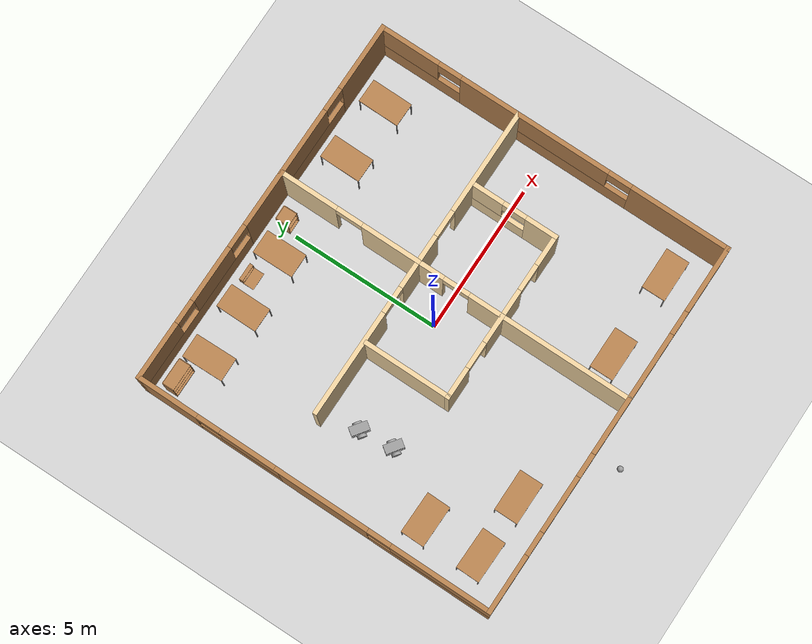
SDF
<sdf version="1.6">
 <world name="default">
  <plugin name="hello" filename="libhello.so"/>
  <light name="sun" type="directional">
   <pose>0 0 10 0 -0 0</pose>
   <diffuse>0.8 0.8 0.8 1</diffuse>
   <specular>0.1 0.1 0.1 1</specular>
   <attenuation>
    <range>1000</range>
    <constant>0.9</constant>
    <linear>0.01</linear>
    <quadratic>0.001</quadratic>
   </attenuation>
   <direction>-0.5 0.5 -1</direction>
  </light>
  <model name="ground_plane">
   <static>1</static>
   <link name="link">
    <collision name="collision">
     <geometry><plane><normal>0 0 1</normal><size>100 100</size></plane></geometry>
     <surface><friction><ode><mu>100</mu><mu2>50</mu2></ode></friction></surface>
    </collision>
    <visual name="visual">
     <cast_shadows>0</cast_shadows>
     <geometry><plane><normal>0 0 1</normal><size>100 100</size></plane></geometry>
     <material>
      <script><uri>file://media/materials/scripts/gazebo.material</uri><name>Gazebo/Grey</name></script>
     </material>
    </visual>
   </link>
  </model>
  <gravity>0 0 -9.8</gravity>
  <magnetic_field>6e-06 2.3e-05 -4.2e-05</magnetic_field>
  <atmosphere type="adiabatic"/>
  <physics name="default_physics" default="0" type="ode">
   <max_step_size>0.001</max_step_size>
   <real_time_factor>1</real_time_factor>
   <real_time_update_rate>1000</real_time_update_rate>
  </physics>
  <scene><ambient>0.4 0.4 0.4 1</ambient><background>0.7 0.7 0.7 1</background><shadows>1</shadows></scene>
  <spherical_coordinates>
   <surface_model>EARTH_WGS84</surface_model>
   <latitude_deg>0</latitude_deg>
   <longitude_deg>0</longitude_deg>
   <elevation>0</elevation>
   <heading_deg>0</heading_deg>
  </spherical_coordinates>
  <model name="building">
   <pose>-0.005642 -0.05216 0 0 -0 1.56564</pose>
   <link name="Wall_40">
    <pose>-2.425 -6.35 0 0 -0 0</pose>
    <visual name="Wall_40_Visual_0">
     <pose>-2.0357 0 1.25 0 -0 0</pose>
     <geometry><box><size>3.42859 0.15 2.5</size></box></geometry>
     <material>
      <script><uri>file://media/materials/scripts/gazebo.material</uri><name>Gazebo/Wood</name></script>
      <ambient>0.921569 0.807843 0.615686 1</ambient>
     </material>
    </visual>
    <collision name="Wall_40_Collision_0">
     <geometry><box><size>3.42859 0.15 2.5</size></box></geometry>
     <pose>-2.0357 0 1.25 0 -0 0</pose>
    </collision>
    <visual name="Wall_40_Visual_1">
     <pose>1.7143 0 0.5 0 -0 0</pose>
     <geometry><box><size>4.07141 0.15 1</size></box></geometry>
     <material>
      <script><uri>file://media/materials/scripts/gazebo.material</uri><name>Gazebo/Wood</name></script>
      <ambient>0.921569 0.807843 0.615686 1</ambient>
     </material>
    </visual>
    <collision name="Wall_40_Collision_1">
     <geometry><box><size>4.07141 0.15 1</size></box></geometry>
     <pose>1.7143 0 0.5 0 -0 0</pose>
    </collision>
    <visual name="Wall_40_Visual_2">
     <pose>2.1143 0 1.75 0 -0 0</pose>
     <geometry><box><size>3.27141 0.15 1.5</size></box></geometry>
     <material>
      <script><uri>file://media/materials/scripts/gazebo.material</uri><name>Gazebo/Wood</name></script>
      <ambient>0.921569 0.807843 0.615686 1</ambient>
     </material>
    </visual>
    <collision name="Wall_40_Collision_2">
     <geometry><box><size>3.27141 0.15 1.5</size></box></geometry>
     <pose>2.1143 0 1.75 0 -0 0</pose>
    </collision>
    <visual name="Wall_40_Visual_3">
     <pose>0.078591 0 2.15 0 -0 0</pose>
     <geometry><box><size>0.8 0.15 0.7</size></box></geometry>
     <material>
      <script><uri>file://media/materials/scripts/gazebo.material</uri><name>Gazebo/Wood</name></script>
      <ambient>0.921569 0.807843 0.615686 1</ambient>
     </material>
    </visual>
    <collision name="Wall_40_Collision_3">
     <geometry><box><size>0.8 0.15 0.7</size></box></geometry>
     <pose>0.078591 0 2.15 0 -0 0</pose>
    </collision>
   </link>
   <link name="Wall_42">
    <pose>1.25 -3.675 0 0 -0 1.5708</pose>
    <visual name="Wall_42_Visual_0">
     <pose>-0.950683 0 1.25 0 -0 0</pose>
     <geometry><box><size>3.59863 0.15 2.5</size></box></geometry>
     <material>
      <script><uri>file://media/materials/scripts/gazebo.material</uri><name>Gazebo/Grey</name></script>
      <ambient>0.921569 0.807843 0.615686 1</ambient>
     </material>
    </visual>
    <collision name="Wall_42_Collision_0">
     <geometry><box><size>3.59863 0.15 2.5</size></box></geometry>
     <pose>-0.950683 0 1.25 0 -0 0</pose>
    </collision>
    <visual name="Wall_42_Visual_1">
     <pose>2.24932 0 1.25 0 -0 0</pose>
     <geometry><box><size>1.00137 0.15 2.5</size></box></geometry>
     <material>
      <script><uri>file://media/materials/scripts/gazebo.material</uri><name>Gazebo/Grey</name></script>
      <ambient>0.921569 0.807843 0.615686 1</ambient>
     </material>
    </visual>
    <collision name="Wall_42_Collision_1">
     <geometry><box><size>1.00137 0.15 2.5</size></box></geometry>
     <pose>2.24932 0 1.25 0 -0 0</pose>
    </collision>
    <visual name="Wall_42_Visual_2">
     <pose>1.29863 0 2.25 0 -0 0</pose>
     <geometry><box><size>0.9 0.15 0.5</size></box></geometry>
     <material>
      <script><uri>file://media/materials/scripts/gazebo.material</uri><name>Gazebo/Grey</name></script>
      <ambient>0.921569 0.807843 0.615686 1</ambient>
     </material>
    </visual>
    <collision name="Wall_42_Collision_2">
     <geometry><box><size>0.9 0.15 0.5</size></box></geometry>
     <pose>1.29863 0 2.25 0 -0 0</pose>
    </collision>
   </link>
   <link name="Wall_44">
    <pose>3.675 -6.35 0 0 -0 0</pose>
    <visual name="Wall_44_Visual_0">
     <pose>-1.44849 0 1.25 0 -0 0</pose>
     <geometry><box><size>2.10302 0.15 2.5</size></box></geometry>
     <material>
      <script><uri>file://media/materials/scripts/gazebo.material</uri><name>Gazebo/Wood</name></script>
      <ambient>0.921569 0.807843 0.615686 1</ambient>
     </material>
    </visual>
    <collision name="Wall_44_Collision_0">
     <geometry><box><size>2.10302 0.15 2.5</size></box></geometry>
     <pose>-1.44849 0 1.25 0 -0 0</pose>
    </collision>
    <visual name="Wall_44_Visual_1">
     <pose>1.05151 0 0.5 0 -0 0</pose>
     <geometry><box><size>2.89698 0.15 1</size></box></geometry>
     <material>
      <script><uri>file://media/materials/scripts/gazebo.material</uri><name>Gazebo/Wood</name></script>
      <ambient>0.921569 0.807843 0.615686 1</ambient>
     </material>
    </visual>
    <collision name="Wall_44_Collision_1">
     <geometry><box><size>2.89698 0.15 1</size></box></geometry>
     <pose>1.05151 0 0.5 0 -0 0</pose>
    </collision>
    <visual name="Wall_44_Visual_2">
     <pose>1.45151 0 1.75 0 -0 0</pose>
     <geometry><box><size>2.09698 0.15 1.5</size></box></geometry>
     <material>
      <script><uri>file://media/materials/scripts/gazebo.material</uri><name>Gazebo/Wood</name></script>
      <ambient>0.921569 0.807843 0.615686 1</ambient>
     </material>
    </visual>
    <collision name="Wall_44_Collision_2">
     <geometry><box><size>2.09698 0.15 1.5</size></box></geometry>
     <pose>1.45151 0 1.75 0 -0 0</pose>
    </collision>
    <visual name="Wall_44_Visual_3">
     <pose>0.003019 0 2.15 0 -0 0</pose>
     <geometry><box><size>0.8 0.15 0.7</size></box></geometry>
     <material>
      <script><uri>file://media/materials/scripts/gazebo.material</uri><name>Gazebo/Wood</name></script>
      <ambient>0.921569 0.807843 0.615686 1</ambient>
     </material>
    </visual>
    <collision name="Wall_44_Collision_3">
     <geometry><box><size>0.8 0.15 0.7</size></box></geometry>
     <pose>0.003019 0 2.15 0 -0 0</pose>
    </collision>
   </link>
   <link name="Wall_46">
    <pose>6.1 -3.675 0 0 -0 1.5708</pose>
    <visual name="Wall_46_Visual_0">
     <pose>-1.57528 0 1.25 0 -0 0</pose>
     <geometry><box><size>2.34944 0.15 2.5</size></box></geometry>
     <material>
      <script><uri>file://media/materials/scripts/gazebo.material</uri><name>Gazebo/Wood</name></script>
      <ambient>0.921569 0.807843 0.615686 1</ambient>
     </material>
    </visual>
    <collision name="Wall_46_Collision_0">
     <geometry><box><size>2.34944 0.15 2.5</size></box></geometry>
     <pose>-1.57528 0 1.25 0 -0 0</pose>
    </collision>
    <visual name="Wall_46_Visual_1">
     <pose>1.17472 0 0.5 0 -0 0</pose>
     <geometry><box><size>3.15056 0.15 1</size></box></geometry>
     <material>
      <script><uri>file://media/materials/scripts/gazebo.material</uri><name>Gazebo/Wood</name></script>
      <ambient>0.921569 0.807843 0.615686 1</ambient>
     </material>
    </visual>
    <collision name="Wall_46_Collision_1">
     <geometry><box><size>3.15056 0.15 1</size></box></geometry>
     <pose>1.17472 0 0.5 0 -0 0</pose>
    </collision>
    <visual name="Wall_46_Visual_2">
     <pose>1.57472 0 1.75 0 -0 0</pose>
     <geometry><box><size>2.35056 0.15 1.5</size></box></geometry>
     <material>
      <script><uri>file://media/materials/scripts/gazebo.material</uri><name>Gazebo/Wood</name></script>
      <ambient>0.921569 0.807843 0.615686 1</ambient>
     </material>
    </visual>
    <collision name="Wall_46_Collision_2">
     <geometry><box><size>2.35056 0.15 1.5</size></box></geometry>
     <pose>1.57472 0 1.75 0 -0 0</pose>
    </collision>
    <visual name="Wall_46_Visual_3">
     <pose>-0.000563 0 2.15 0 -0 0</pose>
     <geometry><box><size>0.8 0.15 0.7</size></box></geometry>
     <material>
      <script><uri>file://media/materials/scripts/gazebo.material</uri><name>Gazebo/Wood</name></script>
      <ambient>0.921569 0.807843 0.615686 1</ambient>
     </material>
    </visual>
    <collision name="Wall_46_Collision_3">
     <geometry><box><size>0.8 0.15 0.7</size></box></geometry>
     <pose>-0.000563 0 2.15 0 -0 0</pose>
    </collision>
   </link>
   <link name="Wall_48">
    <pose>3.67486 -1.00009 0 0 0 -3.14155</pose>
    <visual name="Wall_48_Visual_0">
     <pose>-1.47793 0 1.25 0 -0 0</pose>
     <geometry><box><size>2.04441 0.15 2.5</size></box></geometry>
     <material>
      <script><uri>file://media/materials/scripts/gazebo.material</uri><name>Gazebo/Grey</name></script>
      <ambient>0.921569 0.807843 0.615686 1</ambient>
     </material>
    </visual>
    <collision name="Wall_48_Collision_0">
     <geometry><box><size>2.04441 0.15 2.5</size></box></geometry>
     <pose>-1.47793 0 1.25 0 -0 0</pose>
    </collision>
    <visual name="Wall_48_Visual_1">
     <pose>1.47221 0 1.25 0 -0 0</pose>
     <geometry><box><size>2.05587 0.15 2.5</size></box></geometry>
     <material>
      <script><uri>file://media/materials/scripts/gazebo.material</uri><name>Gazebo/Grey</name></script>
      <ambient>0.921569 0.807843 0.615686 1</ambient>
     </material>
    </visual>
    <collision name="Wall_48_Collision_1">
     <geometry><box><size>2.05587 0.15 2.5</size></box></geometry>
     <pose>1.47221 0 1.25 0 -0 0</pose>
    </collision>
    <visual name="Wall_48_Visual_2">
     <pose>-0.005726 0 2.25 0 -0 0</pose>
     <geometry><box><size>0.9 0.15 0.5</size></box></geometry>
     <material>
      <script><uri>file://media/materials/scripts/gazebo.material</uri><name>Gazebo/Grey</name></script>
      <ambient>0.921569 0.807843 0.615686 1</ambient>
     </material>
    </visual>
    <collision name="Wall_48_Collision_2">
     <geometry><box><size>0.9 0.15 0.5</size></box></geometry>
     <pose>-0.005726 0 2.25 0 -0 0</pose>
    </collision>
   </link>
   <link name="Wall_50">
    <pose>-0.22106 -1.00009 0 0 -0 3.14153</pose>
    <visual name="Wall_50_Visual_0">
     <pose>-1.05843 0 1.25 0 -0 0</pose>
     <geometry><box><size>0.974695 0.15 2.5</size></box></geometry>
     <material>
      <script><uri>file://media/materials/scripts/gazebo.material</uri><name>Gazebo/Grey</name></script>
      <ambient>0.921569 0.807843 0.615686 1</ambient>
     </material>
    </visual>
    <collision name="Wall_50_Collision_0">
     <geometry><box><size>0.974695 0.15 2.5</size></box></geometry>
     <pose>-1.05843 0 1.25 0 -0 0</pose>
    </collision>
    <visual name="Wall_50_Visual_1">
     <pose>0.937348 0 1.25 0 -0 0</pose>
     <geometry><box><size>1.21686 0.15 2.5</size></box></geometry>
     <material>
      <script><uri>file://media/materials/scripts/gazebo.material</uri><name>Gazebo/Grey</name></script>
      <ambient>0.921569 0.807843 0.615686 1</ambient>
     </material>
    </visual>
    <collision name="Wall_50_Collision_1">
     <geometry><box><size>1.21686 0.15 2.5</size></box></geometry>
     <pose>0.937348 0 1.25 0 -0 0</pose>
    </collision>
    <visual name="Wall_50_Visual_2">
     <pose>-0.121083 0 2.25 0 -0 0</pose>
     <geometry><box><size>0.9 0.15 0.5</size></box></geometry>
     <material>
      <script><uri>file://media/materials/scripts/gazebo.material</uri><name>Gazebo/Grey</name></script>
      <ambient>0.921569 0.807843 0.615686 1</ambient>
     </material>
    </visual>
    <collision name="Wall_50_Collision_2">
     <geometry><box><size>0.9 0.15 0.5</size></box></geometry>
     <pose>-0.121083 0 2.25 0 -0 0</pose>
    </collision>
   </link>
   <link name="Wall_52">
    <pose>-1.69184 -2.425 0 0 0 -1.5708</pose>
    <visual name="Wall_52_Visual_0">
     <pose>-0.996807 0 1.25 0 -0 0</pose>
     <geometry><box><size>1.00639 0.15 2.5</size></box></geometry>
     <material>
      <script><uri>file://media/materials/scripts/gazebo.material</uri><name>Gazebo/Grey</name></script>
      <ambient>0.921569 0.807843 0.615686 1</ambient>
     </material>
    </visual>
    <collision name="Wall_52_Collision_0">
     <geometry><box><size>1.00639 0.15 2.5</size></box></geometry>
     <pose>-0.996807 0 1.25 0 -0 0</pose>
    </collision>
    <visual name="Wall_52_Visual_1">
     <pose>0.953193 0 1.25 0 -0 0</pose>
     <geometry><box><size>1.09362 0.15 2.5</size></box></geometry>
     <material>
      <script><uri>file://media/materials/scripts/gazebo.material</uri><name>Gazebo/Grey</name></script>
      <ambient>0.921569 0.807843 0.615686 1</ambient>
     </material>
    </visual>
    <collision name="Wall_52_Collision_1">
     <geometry><box><size>1.09362 0.15 2.5</size></box></geometry>
     <pose>0.953193 0 1.25 0 -0 0</pose>
    </collision>
    <visual name="Wall_52_Visual_2">
     <pose>-0.043615 0 2.25 0 -0 0</pose>
     <geometry><box><size>0.9 0.15 0.5</size></box></geometry>
     <material>
      <script><uri>file://media/materials/scripts/gazebo.material</uri><name>Gazebo/Grey</name></script>
      <ambient>0.921569 0.807843 0.615686 1</ambient>
     </material>
    </visual>
    <collision name="Wall_52_Collision_2">
     <geometry><box><size>0.9 0.15 0.5</size></box></geometry>
     <pose>-0.043615 0 2.25 0 -0 0</pose>
    </collision>
   </link>
   <link name="Wall_54">
    <pose>-0.266839 -3.85 0 0 -0 0</pose>
    <visual name="Wall_54_Visual_0">
     <pose>-0.949915 0 1.25 0 -0 0</pose>
     <geometry><box><size>1.10017 0.15 2.5</size></box></geometry>
     <material>
      <script><uri>file://media/materials/scripts/gazebo.material</uri><name>Gazebo/Grey</name></script>
      <ambient>0.921569 0.807843 0.615686 1</ambient>
     </material>
    </visual>
    <collision name="Wall_54_Collision_0">
     <geometry><box><size>1.10017 0.15 2.5</size></box></geometry>
     <pose>-0.949915 0 1.25 0 -0 0</pose>
    </collision>
    <visual name="Wall_54_Visual_1">
     <pose>0.550085 0 0.5 0 -0 0</pose>
     <geometry><box><size>1.89983 0.15 1</size></box></geometry>
     <material>
      <script><uri>file://media/materials/scripts/gazebo.material</uri><name>Gazebo/Grey</name></script>
      <ambient>0.921569 0.807843 0.615686 1</ambient>
     </material>
    </visual>
    <collision name="Wall_54_Collision_1">
     <geometry><box><size>1.89983 0.15 1</size></box></geometry>
     <pose>0.550085 0 0.5 0 -0 0</pose>
    </collision>
    <visual name="Wall_54_Visual_2">
     <pose>0.950085 0 1.75 0 -0 0</pose>
     <geometry><box><size>1.09983 0.15 1.5</size></box></geometry>
     <material>
      <script><uri>file://media/materials/scripts/gazebo.material</uri><name>Gazebo/Grey</name></script>
      <ambient>0.921569 0.807843 0.615686 1</ambient>
     </material>
    </visual>
    <collision name="Wall_54_Collision_2">
     <geometry><box><size>1.09983 0.15 1.5</size></box></geometry>
     <pose>0.950085 0 1.75 0 -0 0</pose>
    </collision>
    <visual name="Wall_54_Visual_3">
     <pose>0.000171 0 2.15 0 -0 0</pose>
     <geometry><box><size>0.8 0.15 0.7</size></box></geometry>
     <material>
      <script><uri>file://media/materials/scripts/gazebo.material</uri><name>Gazebo/Grey</name></script>
      <ambient>0.921569 0.807843 0.615686 1</ambient>
     </material>
    </visual>
    <collision name="Wall_54_Collision_3">
     <geometry><box><size>0.8 0.15 0.7</size></box></geometry>
     <pose>0.000171 0 2.15 0 -0 0</pose>
    </collision>
   </link>
   <link name="Wall_57">
    <pose>-1.69184 0.425 0 0 -0 1.5708</pose>
    <visual name="Wall_57_Visual_0">
     <pose>-0.995539 0 1.25 0 -0 0</pose>
     <geometry><box><size>1.00892 0.15 2.5</size></box></geometry>
     <material>
      <script><uri>file://media/materials/scripts/gazebo.material</uri><name>Gazebo/Grey</name></script>
      <ambient>0.921569 0.807843 0.615686 1</ambient>
     </material>
    </visual>
    <collision name="Wall_57_Collision_0">
     <geometry><box><size>1.00892 0.15 2.5</size></box></geometry>
     <pose>-0.995539 0 1.25 0 -0 0</pose>
    </collision>
    <visual name="Wall_57_Visual_1">
     <pose>0.954461 0 1.25 0 -0 0</pose>
     <geometry><box><size>1.09108 0.15 2.5</size></box></geometry>
     <material>
      <script><uri>file://media/materials/scripts/gazebo.material</uri><name>Gazebo/Grey</name></script>
      <ambient>0.921569 0.807843 0.615686 1</ambient>
     </material>
    </visual>
    <collision name="Wall_57_Collision_1">
     <geometry><box><size>1.09108 0.15 2.5</size></box></geometry>
     <pose>0.954461 0 1.25 0 -0 0</pose>
    </collision>
    <visual name="Wall_57_Visual_2">
     <pose>-0.041079 0 2.25 0 -0 0</pose>
     <geometry><box><size>0.9 0.15 0.5</size></box></geometry>
     <material>
      <script><uri>file://media/materials/scripts/gazebo.material</uri><name>Gazebo/Grey</name></script>
      <ambient>0.921569 0.807843 0.615686 1</ambient>
     </material>
    </visual>
    <collision name="Wall_57_Collision_2">
     <geometry><box><size>0.9 0.15 0.5</size></box></geometry>
     <pose>-0.041079 0 2.25 0 -0 0</pose>
    </collision>
   </link>
   <link name="Wall_59">
    <collision name="Wall_59_Collision">
     <geometry><box><size>3 0.15 2.5</size></box></geometry>
     <pose>0 0 1.25 0 -0 0</pose>
    </collision>
    <visual name="Wall_59_Visual">
     <pose>0 0 1.25 0 -0 0</pose>
     <geometry><box><size>3 0.15 2.5</size></box></geometry>
     <material>
      <script><uri>file://media/materials/scripts/gazebo.material</uri><name>Gazebo/Grey</name></script>
      <ambient>0.921569 0.807843 0.615686 1</ambient>
     </material>
    </visual>
    <pose>-0.266839 1.85 0 0 -0 0</pose>
   </link>
   <link name="Wall_66">
    <pose>1.24972 1.67482 0 0 -0 1.5708</pose>
    <visual name="Wall_66_Visual_0">
     <pose>-2.24774 0 1.25 0 -0 0</pose>
     <geometry><box><size>1.00452 0.15 2.5</size></box></geometry>
     <material>
      <script><uri>file://media/materials/scripts/gazebo.material</uri><name>Gazebo/Grey</name></script>
      <ambient>0.921569 0.807843 0.615686 1</ambient>
     </material>
    </visual>
    <collision name="Wall_66_Collision_0">
     <geometry><box><size>1.00452 0.15 2.5</size></box></geometry>
     <pose>-2.24774 0 1.25 0 -0 0</pose>
    </collision>
    <visual name="Wall_66_Visual_1">
     <pose>0.952259 0 1.25 0 -0 0</pose>
     <geometry><box><size>3.59548 0.15 2.5</size></box></geometry>
     <material>
      <script><uri>file://media/materials/scripts/gazebo.material</uri><name>Gazebo/Grey</name></script>
      <ambient>0.921569 0.807843 0.615686 1</ambient>
     </material>
    </visual>
    <collision name="Wall_66_Collision_1">
     <geometry><box><size>3.59548 0.15 2.5</size></box></geometry>
     <pose>0.952259 0 1.25 0 -0 0</pose>
    </collision>
    <visual name="Wall_66_Visual_2">
     <pose>-1.29548 0 2.25 0 -0 0</pose>
     <geometry><box><size>0.9 0.15 0.5</size></box></geometry>
     <material>
      <script><uri>file://media/materials/scripts/gazebo.material</uri><name>Gazebo/Grey</name></script>
      <ambient>0.921569 0.807843 0.615686 1</ambient>
     </material>
    </visual>
    <collision name="Wall_66_Collision_2">
     <geometry><box><size>0.9 0.15 0.5</size></box></geometry>
     <pose>-1.29548 0 2.25 0 -0 0</pose>
    </collision>
   </link>
   <link name="Wall_68">
    <pose>6.1 2.675 0 0 -0 1.5708</pose>
    <visual name="Wall_68_Visual_0">
     <pose>-2.7519 0 1.25 0 -0 0</pose>
     <geometry><box><size>1.99621 0.15 2.5</size></box></geometry>
     <material>
      <script><uri>file://media/materials/scripts/gazebo.material</uri><name>Gazebo/Wood</name></script>
      <ambient>0.921569 0.807843 0.615686 1</ambient>
     </material>
    </visual>
    <collision name="Wall_68_Collision_0">
     <geometry><box><size>1.99621 0.15 2.5</size></box></geometry>
     <pose>-2.7519 0 1.25 0 -0 0</pose>
    </collision>
    <visual name="Wall_68_Visual_1">
     <pose>0.998103 0 0.5 0 -0 0</pose>
     <geometry><box><size>5.50379 0.15 1</size></box></geometry>
     <material>
      <script><uri>file://media/materials/scripts/gazebo.material</uri><name>Gazebo/Wood</name></script>
      <ambient>0.921569 0.807843 0.615686 1</ambient>
     </material>
    </visual>
    <collision name="Wall_68_Collision_1">
     <geometry><box><size>5.50379 0.15 1</size></box></geometry>
     <pose>0.998103 0 0.5 0 -0 0</pose>
    </collision>
    <visual name="Wall_68_Visual_2">
     <pose>0.001458 0 1.75 0 -0 0</pose>
     <geometry><box><size>1.9105 0.15 1.5</size></box></geometry>
     <material>
      <script><uri>file://media/materials/scripts/gazebo.material</uri><name>Gazebo/Wood</name></script>
      <ambient>0.921569 0.807843 0.615686 1</ambient>
     </material>
    </visual>
    <collision name="Wall_68_Collision_2">
     <geometry><box><size>1.9105 0.15 1.5</size></box></geometry>
     <pose>0.001458 0 1.75 0 -0 0</pose>
    </collision>
    <visual name="Wall_68_Visual_3">
     <pose>2.75335 0 1.75 0 -0 0</pose>
     <geometry><box><size>1.99329 0.15 1.5</size></box></geometry>
     <material>
      <script><uri>file://media/materials/scripts/gazebo.material</uri><name>Gazebo/Wood</name></script>
      <ambient>0.921569 0.807843 0.615686 1</ambient>
     </material>
    </visual>
    <collision name="Wall_68_Collision_3">
     <geometry><box><size>1.99329 0.15 1.5</size></box></geometry>
     <pose>2.75335 0 1.75 0 -0 0</pose>
    </collision>
    <visual name="Wall_68_Visual_4">
     <pose>-1.35379 0 2.15 0 -0 0</pose>
     <geometry><box><size>0.8 0.15 0.7</size></box></geometry>
     <material>
      <script><uri>file://media/materials/scripts/gazebo.material</uri><name>Gazebo/Wood</name></script>
      <ambient>0.921569 0.807843 0.615686 1</ambient>
     </material>
    </visual>
    <collision name="Wall_68_Collision_4">
     <geometry><box><size>0.8 0.15 0.7</size></box></geometry>
     <pose>-1.35379 0 2.15 0 -0 0</pose>
    </collision>
    <visual name="Wall_68_Visual_5">
     <pose>1.35671 0 2.15 0 -0 0</pose>
     <geometry><box><size>0.8 0.15 0.7</size></box></geometry>
     <material>
      <script><uri>file://media/materials/scripts/gazebo.material</uri><name>Gazebo/Wood</name></script>
      <ambient>0.921569 0.807843 0.615686 1</ambient>
     </material>
    </visual>
    <collision name="Wall_68_Collision_5">
     <geometry><box><size>0.8 0.15 0.7</size></box></geometry>
     <pose>1.35671 0 2.15 0 -0 0</pose>
    </collision>
   </link>
   <link name="Wall_70">
    <pose>3.675 6.35 0 0 -0 3.14159</pose>
    <visual name="Wall_70_Visual_0">
     <pose>-1.43588 0 1.25 0 -0 0</pose>
     <geometry><box><size>2.12825 0.15 2.5</size></box></geometry>
     <material>
      <script><uri>file://media/materials/scripts/gazebo.material</uri><name>Gazebo/Wood</name></script>
      <ambient>0.921569 0.807843 0.615686 1</ambient>
     </material>
    </visual>
    <collision name="Wall_70_Collision_0">
     <geometry><box><size>2.12825 0.15 2.5</size></box></geometry>
     <pose>-1.43588 0 1.25 0 -0 0</pose>
    </collision>
    <visual name="Wall_70_Visual_1">
     <pose>1.06412 0 0.5 0 -0 0</pose>
     <geometry><box><size>2.87175 0.15 1</size></box></geometry>
     <material>
      <script><uri>file://media/materials/scripts/gazebo.material</uri><name>Gazebo/Wood</name></script>
      <ambient>0.921569 0.807843 0.615686 1</ambient>
     </material>
    </visual>
    <collision name="Wall_70_Collision_1">
     <geometry><box><size>2.87175 0.15 1</size></box></geometry>
     <pose>1.06412 0 0.5 0 -0 0</pose>
    </collision>
    <visual name="Wall_70_Visual_2">
     <pose>1.46412 0 1.75 0 -0 0</pose>
     <geometry><box><size>2.07176 0.15 1.5</size></box></geometry>
     <material>
      <script><uri>file://media/materials/scripts/gazebo.material</uri><name>Gazebo/Wood</name></script>
      <ambient>0.921569 0.807843 0.615686 1</ambient>
     </material>
    </visual>
    <collision name="Wall_70_Collision_2">
     <geometry><box><size>2.07176 0.15 1.5</size></box></geometry>
     <pose>1.46412 0 1.75 0 -0 0</pose>
    </collision>
    <visual name="Wall_70_Visual_3">
     <pose>0.028245 0 2.15 0 -0 0</pose>
     <geometry><box><size>0.8 0.15 0.7</size></box></geometry>
     <material>
      <script><uri>file://media/materials/scripts/gazebo.material</uri><name>Gazebo/Wood</name></script>
      <ambient>0.921569 0.807843 0.615686 1</ambient>
     </material>
    </visual>
    <collision name="Wall_70_Collision_3">
     <geometry><box><size>0.8 0.15 0.7</size></box></geometry>
     <pose>0.028245 0 2.15 0 -0 0</pose>
    </collision>
   </link>
   <link name="Wall_72">
    <pose>-2.425 6.35 0 0 -0 3.14159</pose>
    <visual name="Wall_72_Visual_0">
     <pose>-2.13285 0 1.25 0 -0 0</pose>
     <geometry><box><size>3.2343 0.15 2.5</size></box></geometry>
     <material>
      <script><uri>file://media/materials/scripts/gazebo.material</uri><name>Gazebo/Wood</name></script>
      <ambient>0.921569 0.807843 0.615686 1</ambient>
     </material>
    </visual>
    <collision name="Wall_72_Collision_0">
     <geometry><box><size>3.2343 0.15 2.5</size></box></geometry>
     <pose>-2.13285 0 1.25 0 -0 0</pose>
    </collision>
    <visual name="Wall_72_Visual_1">
     <pose>1.61715 0 0.5 0 -0 0</pose>
     <geometry><box><size>4.2657 0.15 1</size></box></geometry>
     <material>
      <script><uri>file://media/materials/scripts/gazebo.material</uri><name>Gazebo/Wood</name></script>
      <ambient>0.921569 0.807843 0.615686 1</ambient>
     </material>
    </visual>
    <collision name="Wall_72_Collision_1">
     <geometry><box><size>4.2657 0.15 1</size></box></geometry>
     <pose>1.61715 0 0.5 0 -0 0</pose>
    </collision>
    <visual name="Wall_72_Visual_2">
     <pose>2.01715 0 1.75 0 -0 0</pose>
     <geometry><box><size>3.4657 0.15 1.5</size></box></geometry>
     <material>
      <script><uri>file://media/materials/scripts/gazebo.material</uri><name>Gazebo/Wood</name></script>
      <ambient>0.921569 0.807843 0.615686 1</ambient>
     </material>
    </visual>
    <collision name="Wall_72_Collision_2">
     <geometry><box><size>3.4657 0.15 1.5</size></box></geometry>
     <pose>2.01715 0 1.75 0 -0 0</pose>
    </collision>
    <visual name="Wall_72_Visual_3">
     <pose>-0.115701 0 2.15 0 -0 0</pose>
     <geometry><box><size>0.8 0.15 0.7</size></box></geometry>
     <material>
      <script><uri>file://media/materials/scripts/gazebo.material</uri><name>Gazebo/Wood</name></script>
      <ambient>0.921569 0.807843 0.615686 1</ambient>
     </material>
    </visual>
    <collision name="Wall_72_Collision_3">
     <geometry><box><size>0.8 0.15 0.7</size></box></geometry>
     <pose>-0.115701 0 2.15 0 -0 0</pose>
    </collision>
   </link>
   <link name="Wall_74">
    <pose>-6.1 2.675 0 0 0 -1.5708</pose>
    <visual name="Wall_74_Visual_0">
     <pose>-2.74951 0 1.25 0 -0 0</pose>
     <geometry><box><size>2.00098 0.15 2.5</size></box></geometry>
     <material>
      <script><uri>file://media/materials/scripts/gazebo.material</uri><name>Gazebo/Wood</name></script>
      <ambient>0.921569 0.807843 0.615686 1</ambient>
     </material>
    </visual>
    <collision name="Wall_74_Collision_0">
     <geometry><box><size>2.00098 0.15 2.5</size></box></geometry>
     <pose>-2.74951 0 1.25 0 -0 0</pose>
    </collision>
    <visual name="Wall_74_Visual_1">
     <pose>1.00049 0 0.5 0 -0 0</pose>
     <geometry><box><size>5.49902 0.15 1</size></box></geometry>
     <material>
      <script><uri>file://media/materials/scripts/gazebo.material</uri><name>Gazebo/Wood</name></script>
      <ambient>0.921569 0.807843 0.615686 1</ambient>
     </material>
    </visual>
    <collision name="Wall_74_Collision_1">
     <geometry><box><size>5.49902 0.15 1</size></box></geometry>
     <pose>1.00049 0 0.5 0 -0 0</pose>
    </collision>
    <visual name="Wall_74_Visual_2">
     <pose>0.005454 0 1.75 0 -0 0</pose>
     <geometry><box><size>1.90894 0.15 1.5</size></box></geometry>
     <material>
      <script><uri>file://media/materials/scripts/gazebo.material</uri><name>Gazebo/Wood</name></script>
      <ambient>0.921569 0.807843 0.615686 1</ambient>
     </material>
    </visual>
    <collision name="Wall_74_Collision_2">
     <geometry><box><size>1.90894 0.15 1.5</size></box></geometry>
     <pose>0.005454 0 1.75 0 -0 0</pose>
    </collision>
    <visual name="Wall_74_Visual_3">
     <pose>2.75496 0 1.75 0 -0 0</pose>
     <geometry><box><size>1.99008 0.15 1.5</size></box></geometry>
     <material>
      <script><uri>file://media/materials/scripts/gazebo.material</uri><name>Gazebo/Wood</name></script>
      <ambient>0.921569 0.807843 0.615686 1</ambient>
     </material>
    </visual>
    <collision name="Wall_74_Collision_3">
     <geometry><box><size>1.99008 0.15 1.5</size></box></geometry>
     <pose>2.75496 0 1.75 0 -0 0</pose>
    </collision>
    <visual name="Wall_74_Visual_4">
     <pose>-1.34902 0 2.15 0 -0 0</pose>
     <geometry><box><size>0.8 0.15 0.7</size></box></geometry>
     <material>
      <script><uri>file://media/materials/scripts/gazebo.material</uri><name>Gazebo/Wood</name></script>
      <ambient>0.921569 0.807843 0.615686 1</ambient>
     </material>
    </visual>
    <collision name="Wall_74_Collision_4">
     <geometry><box><size>0.8 0.15 0.7</size></box></geometry>
     <pose>-1.34902 0 2.15 0 -0 0</pose>
    </collision>
    <visual name="Wall_74_Visual_5">
     <pose>1.35992 0 2.15 0 -0 0</pose>
     <geometry><box><size>0.8 0.15 0.7</size></box></geometry>
     <material>
      <script><uri>file://media/materials/scripts/gazebo.material</uri><name>Gazebo/Wood</name></script>
      <ambient>0.921569 0.807843 0.615686 1</ambient>
     </material>
    </visual>
    <collision name="Wall_74_Collision_5">
     <geometry><box><size>0.8 0.15 0.7</size></box></geometry>
     <pose>1.35992 0 2.15 0 -0 0</pose>
    </collision>
   </link>
   <link name="Wall_76">
    <collision name="Wall_76_Collision">
     <geometry><box><size>4.5 0.15 2.5</size></box></geometry>
     <pose>0 0 1.25 0 -0 0</pose>
    </collision>
    <visual name="Wall_76_Visual">
     <pose>0 0 1.25 0 -0 0</pose>
     <geometry><box><size>4.5 0.15 2.5</size></box></geometry>
     <material>
      <script><uri>file://media/materials/scripts/gazebo.material</uri><name>Gazebo/Grey</name></script>
      <ambient>0.921569 0.807843 0.615686 1</ambient>
     </material>
    </visual>
    <pose>-3.925 -1 0 0 -0 0</pose>
   </link>
   <link name="Wall_78">
    <pose>-6.1 -3.675 0 0 0 -1.5708</pose>
    <visual name="Wall_78_Visual_0">
     <pose>-1.5652 0 1.25 0 -0 0</pose>
     <geometry><box><size>2.36961 0.15 2.5</size></box></geometry>
     <material>
      <script><uri>file://media/materials/scripts/gazebo.material</uri><name>Gazebo/Wood</name></script>
      <ambient>0.921569 0.807843 0.615686 1</ambient>
     </material>
    </visual>
    <collision name="Wall_78_Collision_0">
     <geometry><box><size>2.36961 0.15 2.5</size></box></geometry>
     <pose>-1.5652 0 1.25 0 -0 0</pose>
    </collision>
    <visual name="Wall_78_Visual_1">
     <pose>1.1848 0 0.5 0 -0 0</pose>
     <geometry><box><size>3.13039 0.15 1</size></box></geometry>
     <material>
      <script><uri>file://media/materials/scripts/gazebo.material</uri><name>Gazebo/Wood</name></script>
      <ambient>0.921569 0.807843 0.615686 1</ambient>
     </material>
    </visual>
    <collision name="Wall_78_Collision_1">
     <geometry><box><size>3.13039 0.15 1</size></box></geometry>
     <pose>1.1848 0 0.5 0 -0 0</pose>
    </collision>
    <visual name="Wall_78_Visual_2">
     <pose>1.5848 0 1.75 0 -0 0</pose>
     <geometry><box><size>2.33039 0.15 1.5</size></box></geometry>
     <material>
      <script><uri>file://media/materials/scripts/gazebo.material</uri><name>Gazebo/Wood</name></script>
      <ambient>0.921569 0.807843 0.615686 1</ambient>
     </material>
    </visual>
    <collision name="Wall_78_Collision_2">
     <geometry><box><size>2.33039 0.15 1.5</size></box></geometry>
     <pose>1.5848 0 1.75 0 -0 0</pose>
    </collision>
    <visual name="Wall_78_Visual_3">
     <pose>0.019608 0 2.15 0 -0 0</pose>
     <geometry><box><size>0.8 0.15 0.7</size></box></geometry>
     <material>
      <script><uri>file://media/materials/scripts/gazebo.material</uri><name>Gazebo/Wood</name></script>
      <ambient>0.921569 0.807843 0.615686 1</ambient>
     </material>
    </visual>
    <collision name="Wall_78_Collision_3">
     <geometry><box><size>0.8 0.15 0.7</size></box></geometry>
     <pose>0.019608 0 2.15 0 -0 0</pose>
    </collision>
   </link>
   <static>1</static>
  </model>
  <model name="Robot">
   <link name="link_0">
    <pose>0.0375 0 -0.0375 0 -0 0</pose>
    <inertial>
     <mass>1</mass>
     <inertia>
      <ixx>0.166667</ixx>
      <ixy>0</ixy>
      <ixz>0</ixz>
      <iyy>0.166667</iyy>
      <iyz>0</iyz>
      <izz>0.166667</izz>
     </inertia>
    </inertial>
    <visual name="visual">
     <geometry><box><size>0.6 0.3 0.1</size></box></geometry>
     <material>
      <lighting>1</lighting>
      <script><uri>file://media/materials/scripts/gazebo.material</uri><name>Gazebo/Grey</name></script>
      <ambient>0.3 0.3 0.3 1</ambient>
      <diffuse>0.7 0.7 0.7 1</diffuse>
      <specular>0.01 0.01 0.01 1</specular>
      <emissive>0 0 0 1</emissive>
      <shader type="vertex"><normal_map>__default__</normal_map></shader>
     </material>
    </visual>
    <collision name="collision">
     <geometry><box><size>0.6 0.3 0.1</size></box></geometry>
     <surface>
      <friction>
       <ode><mu>1</mu><mu2>1</mu2><fdir1>0 0 0</fdir1><slip1>0</slip1><slip2>0</slip2></ode>
       <torsional>
        <coefficient>1</coefficient>
        <patch_radius>0</patch_radius>
        <surface_radius>0</surface_radius>
        <use_patch_radius>1</use_patch_radius>
        <ode><slip>0</slip></ode>
       </torsional>
      </friction>
      <bounce><restitution_coefficient>0</restitution_coefficient><threshold>1e+06</threshold></bounce>
      <contact>
       <collide_without_contact>0</collide_without_contact>
       <collide_without_contact_bitmask>1</collide_without_contact_bitmask>
       <collide_bitmask>1</collide_bitmask>
       <ode>
        <soft_cfm>0</soft_cfm>
        <soft_erp>0.2</soft_erp>
        <kp>1e+13</kp>
        <kd>1</kd>
        <max_vel>0.01</max_vel>
        <min_depth>0</min_depth>
       </ode>
       <bullet>
        <split_impulse>1</split_impulse>
        <split_impulse_penetration_threshold>-0.01</split_impulse_penetration_threshold>
        <soft_cfm>0</soft_cfm>
        <soft_erp>0.2</soft_erp>
        <kp>1e+13</kp>
        <kd>1</kd>
       </bullet>
      </contact>
     </surface>
    </collision>
   </link>
   <link name="link_0_clone">
    <pose>0.0375 0 0.2625 0 -0 0</pose>
    <inertial>
     <mass>1</mass>
     <inertia>
      <ixx>0.166667</ixx>
      <ixy>0</ixy>
      <ixz>0</ixz>
      <iyy>0.166667</iyy>
      <iyz>0</iyz>
      <izz>0.166667</izz>
     </inertia>
    </inertial>
    <visual name="visual">
     <geometry><box><size>0.6 0.3 0.1</size></box></geometry>
     <material>
      <lighting>1</lighting>
      <script><uri>file://media/materials/scripts/gazebo.material</uri><name>Gazebo/Grey</name></script>
      <ambient>0.3 0.3 0.3 1</ambient>
      <diffuse>0.7 0.7 0.7 1</diffuse>
      <specular>0.01 0.01 0.01 1</specular>
      <emissive>0 0 0 1</emissive>
      <shader type="vertex"><normal_map>__default__</normal_map></shader>
     </material>
    </visual>
    <collision name="collision">
     <geometry><box><size>0.6 0.3 0.1</size></box></geometry>
     <surface>
      <friction>
       <ode><mu>1</mu><mu2>1</mu2><fdir1>0 0 0</fdir1><slip1>0</slip1><slip2>0</slip2></ode>
       <torsional>
        <coefficient>1</coefficient>
        <patch_radius>0</patch_radius>
        <surface_radius>0</surface_radius>
        <use_patch_radius>1</use_patch_radius>
        <ode><slip>0</slip></ode>
       </torsional>
      </friction>
      <bounce><restitution_coefficient>0</restitution_coefficient><threshold>1e+06</threshold></bounce>
      <contact>
       <collide_without_contact>0</collide_without_contact>
       <collide_without_contact_bitmask>1</collide_without_contact_bitmask>
       <collide_bitmask>1</collide_bitmask>
       <ode>
        <soft_cfm>0</soft_cfm>
        <soft_erp>0.2</soft_erp>
        <kp>1e+13</kp>
        <kd>1</kd>
        <max_vel>0.01</max_vel>
        <min_depth>0</min_depth>
       </ode>
       <bullet>
        <split_impulse>1</split_impulse>
        <split_impulse_penetration_threshold>-0.01</split_impulse_penetration_threshold>
        <soft_cfm>0</soft_cfm>
        <soft_erp>0.2</soft_erp>
        <kp>1e+13</kp>
        <kd>1</kd>
       </bullet>
      </contact>
     </surface>
    </collision>
   </link>
   <link name="link_1">
    <pose>0.0375 0 0.1125 0 -0 0</pose>
    <inertial>
     <mass>1</mass>
     <inertia>
      <ixx>0.166667</ixx>
      <ixy>0</ixy>
      <ixz>0</ixz>
      <iyy>0.166667</iyy>
      <iyz>0</iyz>
      <izz>0.166667</izz>
     </inertia>
    </inertial>
    <visual name="visual">
     <geometry><box><size>0.55 0.25 0.2</size></box></geometry>
     <material>
      <lighting>1</lighting>
      <script><uri>file://media/materials/scripts/gazebo.material</uri><name>Gazebo/Grey</name></script>
      <ambient>0.3 0.3 0.3 1</ambient>
      <diffuse>0.7 0.7 0.7 1</diffuse>
      <specular>0.01 0.01 0.01 1</specular>
      <emissive>0 0 0 1</emissive>
      <shader type="vertex"><normal_map>__default__</normal_map></shader>
     </material>
    </visual>
    <collision name="collision">
     <geometry><box><size>0.55 0.25 0.2</size></box></geometry>
     <surface>
      <friction>
       <ode><mu>1</mu><mu2>1</mu2><fdir1>0 0 0</fdir1><slip1>0</slip1><slip2>0</slip2></ode>
       <torsional>
        <coefficient>1</coefficient>
        <patch_radius>0</patch_radius>
        <surface_radius>0</surface_radius>
        <use_patch_radius>1</use_patch_radius>
        <ode><slip>0</slip></ode>
       </torsional>
      </friction>
      <bounce><restitution_coefficient>0</restitution_coefficient><threshold>1e+06</threshold></bounce>
      <contact>
       <collide_without_contact>0</collide_without_contact>
       <collide_without_contact_bitmask>1</collide_without_contact_bitmask>
       <collide_bitmask>1</collide_bitmask>
       <ode>
        <soft_cfm>0</soft_cfm>
        <soft_erp>0.2</soft_erp>
        <kp>1e+13</kp>
        <kd>1</kd>
        <max_vel>0.01</max_vel>
        <min_depth>0</min_depth>
       </ode>
       <bullet>
        <split_impulse>1</split_impulse>
        <split_impulse_penetration_threshold>-0.01</split_impulse_penetration_threshold>
        <soft_cfm>0</soft_cfm>
        <soft_erp>0.2</soft_erp>
        <kp>1e+13</kp>
        <kd>1</kd>
       </bullet>
      </contact>
     </surface>
    </collision>
   </link>
   <link name="link_2">
    <pose>0.0375 -0.200014 -0.0875 1.5707 -0 0</pose>
    <inertial>
     <mass>1</mass>
     <inertia><ixx>0.145833</ixx><ixy>0</ixy><ixz>0</ixz><iyy>0.145833</iyy><iyz>0</iyz><izz>0.125</izz></inertia>
    </inertial>
    <visual name="visual">
     <geometry><cylinder><radius>0.15</radius><length>0.1</length></cylinder></geometry>
     <material>
      <lighting>1</lighting>
      <script><uri>file://media/materials/scripts/gazebo.material</uri><name>Gazebo/Grey</name></script>
      <ambient>0.3 0.3 0.3 1</ambient>
      <diffuse>0.7 0.7 0.7 1</diffuse>
      <specular>0.01 0.01 0.01 1</specular>
      <emissive>0 0 0 1</emissive>
      <shader type="vertex"><normal_map>__default__</normal_map></shader>
     </material>
    </visual>
    <collision name="collision">
     <geometry><cylinder><radius>0.15</radius><length>0.1</length></cylinder></geometry>
     <surface>
      <friction>
       <ode><mu>1</mu><mu2>1</mu2><fdir1>0 0 0</fdir1><slip1>0</slip1><slip2>0</slip2></ode>
       <torsional>
        <coefficient>1</coefficient>
        <patch_radius>0</patch_radius>
        <surface_radius>0</surface_radius>
        <use_patch_radius>1</use_patch_radius>
        <ode><slip>0</slip></ode>
       </torsional>
      </friction>
      <bounce><restitution_coefficient>0</restitution_coefficient><threshold>1e+06</threshold></bounce>
      <contact>
       <collide_without_contact>0</collide_without_contact>
       <collide_without_contact_bitmask>1</collide_without_contact_bitmask>
       <collide_bitmask>1</collide_bitmask>
       <ode>
        <soft_cfm>0</soft_cfm>
        <soft_erp>0.2</soft_erp>
        <kp>1e+13</kp>
        <kd>1</kd>
        <max_vel>0.01</max_vel>
        <min_depth>0</min_depth>
       </ode>
       <bullet>
        <split_impulse>1</split_impulse>
        <split_impulse_penetration_threshold>-0.01</split_impulse_penetration_threshold>
        <soft_cfm>0</soft_cfm>
        <soft_erp>0.2</soft_erp>
        <kp>1e+13</kp>
        <kd>1</kd>
       </bullet>
      </contact>
     </surface>
    </collision>
   </link>
   <link name="link_2_clone">
    <pose>0.0375 0.200014 -0.0875 1.5707 -0 0</pose>
    <inertial>
     <mass>1</mass>
     <inertia><ixx>0.145833</ixx><ixy>0</ixy><ixz>0</ixz><iyy>0.145833</iyy><iyz>0</iyz><izz>0.125</izz></inertia>
    </inertial>
    <visual name="visual">
     <geometry><cylinder><radius>0.15</radius><length>0.1</length></cylinder></geometry>
     <material>
      <lighting>1</lighting>
      <script><uri>file://media/materials/scripts/gazebo.material</uri><name>Gazebo/Grey</name></script>
      <ambient>0.3 0.3 0.3 1</ambient>
      <diffuse>0.7 0.7 0.7 1</diffuse>
      <specular>0.01 0.01 0.01 1</specular>
      <emissive>0 0 0 1</emissive>
      <shader type="vertex"><normal_map>__default__</normal_map></shader>
     </material>
    </visual>
    <collision name="collision">
     <geometry><cylinder><radius>0.15</radius><length>0.1</length></cylinder></geometry>
     <surface>
      <friction>
       <ode><mu>1</mu><mu2>1</mu2><fdir1>0 0 0</fdir1><slip1>0</slip1><slip2>0</slip2></ode>
       <torsional>
        <coefficient>1</coefficient>
        <patch_radius>0</patch_radius>
        <surface_radius>0</surface_radius>
        <use_patch_radius>1</use_patch_radius>
        <ode><slip>0</slip></ode>
       </torsional>
      </friction>
      <bounce><restitution_coefficient>0</restitution_coefficient><threshold>1e+06</threshold></bounce>
      <contact>
       <collide_without_contact>0</collide_without_contact>
       <collide_without_contact_bitmask>1</collide_without_contact_bitmask>
       <collide_bitmask>1</collide_bitmask>
       <ode>
        <soft_cfm>0</soft_cfm>
        <soft_erp>0.2</soft_erp>
        <kp>1e+13</kp>
        <kd>1</kd>
        <max_vel>0.01</max_vel>
        <min_depth>0</min_depth>
       </ode>
       <bullet>
        <split_impulse>1</split_impulse>
        <split_impulse_penetration_threshold>-0.01</split_impulse_penetration_threshold>
        <soft_cfm>0</soft_cfm>
        <soft_erp>0.2</soft_erp>
        <kp>1e+13</kp>
        <kd>1</kd>
       </bullet>
      </contact>
     </surface>
    </collision>
   </link>
   <link name="link_3">
    <pose>-0.1875 0 -0.1625 0 -0 0</pose>
    <inertial>
     <mass>1</mass>
     <inertia><ixx>0.1</ixx><ixy>0</ixy><ixz>0</ixz><iyy>0.1</iyy><iyz>0</iyz><izz>0.1</izz></inertia>
    </inertial>
    <visual name="visual">
     <geometry><sphere><radius>0.075</radius></sphere></geometry>
     <material>
      <lighting>1</lighting>
      <script><uri>file://media/materials/scripts/gazebo.material</uri><name>Gazebo/Grey</name></script>
      <ambient>0.3 0.3 0.3 1</ambient>
      <diffuse>0.7 0.7 0.7 1</diffuse>
      <specular>0.01 0.01 0.01 1</specular>
      <emissive>0 0 0 1</emissive>
      <shader type="vertex"><normal_map>__default__</normal_map></shader>
     </material>
    </visual>
    <collision name="collision">
     <geometry><sphere><radius>0.075</radius></sphere></geometry>
     <surface>
      <friction>
       <ode><mu>1</mu><mu2>1</mu2><fdir1>0 0 0</fdir1><slip1>0</slip1><slip2>0</slip2></ode>
       <torsional>
        <coefficient>1</coefficient>
        <patch_radius>0</patch_radius>
        <surface_radius>0</surface_radius>
        <use_patch_radius>1</use_patch_radius>
        <ode><slip>0</slip></ode>
       </torsional>
      </friction>
      <bounce><restitution_coefficient>0</restitution_coefficient><threshold>1e+06</threshold></bounce>
      <contact>
       <collide_without_contact>0</collide_without_contact>
       <collide_without_contact_bitmask>1</collide_without_contact_bitmask>
       <collide_bitmask>1</collide_bitmask>
       <ode>
        <soft_cfm>0</soft_cfm>
        <soft_erp>0.2</soft_erp>
        <kp>1e+13</kp>
        <kd>1</kd>
        <max_vel>0.01</max_vel>
        <min_depth>0</min_depth>
       </ode>
       <bullet>
        <split_impulse>1</split_impulse>
        <split_impulse_penetration_threshold>-0.01</split_impulse_penetration_threshold>
        <soft_cfm>0</soft_cfm>
        <soft_erp>0.2</soft_erp>
        <kp>1e+13</kp>
        <kd>1</kd>
       </bullet>
      </contact>
     </surface>
    </collision>
   </link>
   <joint name="link_0_JOINT_0" type="fixed">
    <parent>link_0</parent>
    <child>link_1</child>
    <physics>
     <ode><limit><cfm>0</cfm><erp>0.2</erp></limit><suspension><cfm>0</cfm><erp>0.2</erp></suspension></ode>
    </physics>
   </joint>
   <joint name="link_0_JOINT_2" type="revolute">
    <parent>link_0</parent>
    <child>link_2</child>
    <axis>
     <xyz>0 0 1</xyz>
     <use_parent_model_frame>0</use_parent_model_frame>
     <limit>
      <lower>-1.79769e+308</lower>
      <upper>1.79769e+308</upper>
      <effort>-1</effort>
      <velocity>-1</velocity>
     </limit>
     <dynamics>
      <spring_reference>0</spring_reference>
      <spring_stiffness>0</spring_stiffness>
      <damping>0</damping>
     </dynamics>
    </axis>
    <physics>
     <ode><limit><cfm>0</cfm><erp>0.2</erp></limit><suspension><cfm>0</cfm><erp>0.2</erp></suspension></ode>
    </physics>
   </joint>
   <joint name="link_0_JOINT_3" type="revolute">
    <parent>link_0</parent>
    <child>link_2_clone</child>
    <axis>
     <xyz>0 0 1</xyz>
     <use_parent_model_frame>0</use_parent_model_frame>
     <limit>
      <lower>-1.79769e+308</lower>
      <upper>1.79769e+308</upper>
      <effort>-1</effort>
      <velocity>-1</velocity>
     </limit>
     <dynamics>
      <spring_reference>0</spring_reference>
      <spring_stiffness>0</spring_stiffness>
      <damping>0</damping>
     </dynamics>
    </axis>
    <physics>
     <ode><limit><cfm>0</cfm><erp>0.2</erp></limit><suspension><cfm>0</cfm><erp>0.2</erp></suspension></ode>
    </physics>
   </joint>
   <joint name="link_0_JOINT_4" type="ball">
    <parent>link_0</parent>
    <child>link_3</child>
    <physics>
     <ode><limit><cfm>0</cfm><erp>0.2</erp></limit><suspension><cfm>0</cfm><erp>0.2</erp></suspension></ode>
    </physics>
   </joint>
   <joint name="link_1_JOINT_1" type="fixed">
    <parent>link_1</parent>
    <child>link_0_clone</child>
    <physics>
     <ode><limit><cfm>0</cfm><erp>0.2</erp></limit><suspension><cfm>0</cfm><erp>0.2</erp></suspension></ode>
    </physics>
   </joint>
   <static>0</static>
   <pose>-3.90605 0.122373 0.237504 4e-06 -1.4e-05 -0.622999</pose>
  </model>
  <model name="Robot_0">
   <link name="link_0">
    <pose>0.0375 0 -0.0375 0 -0 0</pose>
    <inertial>
     <mass>1</mass>
     <inertia>
      <ixx>0.166667</ixx>
      <ixy>0</ixy>
      <ixz>0</ixz>
      <iyy>0.166667</iyy>
      <iyz>0</iyz>
      <izz>0.166667</izz>
     </inertia>
    </inertial>
    <visual name="visual">
     <geometry><box><size>0.6 0.3 0.1</size></box></geometry>
     <material>
      <lighting>1</lighting>
      <script><uri>file://media/materials/scripts/gazebo.material</uri><name>Gazebo/Grey</name></script>
      <ambient>0.3 0.3 0.3 1</ambient>
      <diffuse>0.7 0.7 0.7 1</diffuse>
      <specular>0.01 0.01 0.01 1</specular>
      <emissive>0 0 0 1</emissive>
      <shader type="vertex"><normal_map>__default__</normal_map></shader>
     </material>
    </visual>
    <collision name="collision">
     <geometry><box><size>0.6 0.3 0.1</size></box></geometry>
     <surface>
      <friction>
       <ode><mu>1</mu><mu2>1</mu2><fdir1>0 0 0</fdir1><slip1>0</slip1><slip2>0</slip2></ode>
       <torsional>
        <coefficient>1</coefficient>
        <patch_radius>0</patch_radius>
        <surface_radius>0</surface_radius>
        <use_patch_radius>1</use_patch_radius>
        <ode><slip>0</slip></ode>
       </torsional>
      </friction>
      <bounce><restitution_coefficient>0</restitution_coefficient><threshold>1e+06</threshold></bounce>
      <contact>
       <collide_without_contact>0</collide_without_contact>
       <collide_without_contact_bitmask>1</collide_without_contact_bitmask>
       <collide_bitmask>1</collide_bitmask>
       <ode>
        <soft_cfm>0</soft_cfm>
        <soft_erp>0.2</soft_erp>
        <kp>1e+13</kp>
        <kd>1</kd>
        <max_vel>0.01</max_vel>
        <min_depth>0</min_depth>
       </ode>
       <bullet>
        <split_impulse>1</split_impulse>
        <split_impulse_penetration_threshold>-0.01</split_impulse_penetration_threshold>
        <soft_cfm>0</soft_cfm>
        <soft_erp>0.2</soft_erp>
        <kp>1e+13</kp>
        <kd>1</kd>
       </bullet>
      </contact>
     </surface>
    </collision>
   </link>
   <link name="link_0_clone">
    <pose>0.0375 0 0.2625 0 -0 0</pose>
    <inertial>
     <mass>1</mass>
     <inertia>
      <ixx>0.166667</ixx>
      <ixy>0</ixy>
      <ixz>0</ixz>
      <iyy>0.166667</iyy>
      <iyz>0</iyz>
      <izz>0.166667</izz>
     </inertia>
    </inertial>
    <visual name="visual">
     <geometry><box><size>0.6 0.3 0.1</size></box></geometry>
     <material>
      <lighting>1</lighting>
      <script><uri>file://media/materials/scripts/gazebo.material</uri><name>Gazebo/Grey</name></script>
      <ambient>0.3 0.3 0.3 1</ambient>
      <diffuse>0.7 0.7 0.7 1</diffuse>
      <specular>0.01 0.01 0.01 1</specular>
      <emissive>0 0 0 1</emissive>
      <shader type="vertex"><normal_map>__default__</normal_map></shader>
     </material>
    </visual>
    <collision name="collision">
     <geometry><box><size>0.6 0.3 0.1</size></box></geometry>
     <surface>
      <friction>
       <ode><mu>1</mu><mu2>1</mu2><fdir1>0 0 0</fdir1><slip1>0</slip1><slip2>0</slip2></ode>
       <torsional>
        <coefficient>1</coefficient>
        <patch_radius>0</patch_radius>
        <surface_radius>0</surface_radius>
        <use_patch_radius>1</use_patch_radius>
        <ode><slip>0</slip></ode>
       </torsional>
      </friction>
      <bounce><restitution_coefficient>0</restitution_coefficient><threshold>1e+06</threshold></bounce>
      <contact>
       <collide_without_contact>0</collide_without_contact>
       <collide_without_contact_bitmask>1</collide_without_contact_bitmask>
       <collide_bitmask>1</collide_bitmask>
       <ode>
        <soft_cfm>0</soft_cfm>
        <soft_erp>0.2</soft_erp>
        <kp>1e+13</kp>
        <kd>1</kd>
        <max_vel>0.01</max_vel>
        <min_depth>0</min_depth>
       </ode>
       <bullet>
        <split_impulse>1</split_impulse>
        <split_impulse_penetration_threshold>-0.01</split_impulse_penetration_threshold>
        <soft_cfm>0</soft_cfm>
        <soft_erp>0.2</soft_erp>
        <kp>1e+13</kp>
        <kd>1</kd>
       </bullet>
      </contact>
     </surface>
    </collision>
   </link>
   <link name="link_1">
    <pose>0.0375 0 0.1125 0 -0 0</pose>
    <inertial>
     <mass>1</mass>
     <inertia>
      <ixx>0.166667</ixx>
      <ixy>0</ixy>
      <ixz>0</ixz>
      <iyy>0.166667</iyy>
      <iyz>0</iyz>
      <izz>0.166667</izz>
     </inertia>
    </inertial>
    <visual name="visual">
     <geometry><box><size>0.55 0.25 0.2</size></box></geometry>
     <material>
      <lighting>1</lighting>
      <script><uri>file://media/materials/scripts/gazebo.material</uri><name>Gazebo/Grey</name></script>
      <ambient>0.3 0.3 0.3 1</ambient>
      <diffuse>0.7 0.7 0.7 1</diffuse>
      <specular>0.01 0.01 0.01 1</specular>
      <emissive>0 0 0 1</emissive>
      <shader type="vertex"><normal_map>__default__</normal_map></shader>
     </material>
    </visual>
    <collision name="collision">
     <geometry><box><size>0.55 0.25 0.2</size></box></geometry>
     <surface>
      <friction>
       <ode><mu>1</mu><mu2>1</mu2><fdir1>0 0 0</fdir1><slip1>0</slip1><slip2>0</slip2></ode>
       <torsional>
        <coefficient>1</coefficient>
        <patch_radius>0</patch_radius>
        <surface_radius>0</surface_radius>
        <use_patch_radius>1</use_patch_radius>
        <ode><slip>0</slip></ode>
       </torsional>
      </friction>
      <bounce><restitution_coefficient>0</restitution_coefficient><threshold>1e+06</threshold></bounce>
      <contact>
       <collide_without_contact>0</collide_without_contact>
       <collide_without_contact_bitmask>1</collide_without_contact_bitmask>
       <collide_bitmask>1</collide_bitmask>
       <ode>
        <soft_cfm>0</soft_cfm>
        <soft_erp>0.2</soft_erp>
        <kp>1e+13</kp>
        <kd>1</kd>
        <max_vel>0.01</max_vel>
        <min_depth>0</min_depth>
       </ode>
       <bullet>
        <split_impulse>1</split_impulse>
        <split_impulse_penetration_threshold>-0.01</split_impulse_penetration_threshold>
        <soft_cfm>0</soft_cfm>
        <soft_erp>0.2</soft_erp>
        <kp>1e+13</kp>
        <kd>1</kd>
       </bullet>
      </contact>
     </surface>
    </collision>
   </link>
   <link name="link_2">
    <pose>0.0375 -0.200014 -0.0875 1.5707 -0 0</pose>
    <inertial>
     <mass>1</mass>
     <inertia><ixx>0.145833</ixx><ixy>0</ixy><ixz>0</ixz><iyy>0.145833</iyy><iyz>0</iyz><izz>0.125</izz></inertia>
    </inertial>
    <visual name="visual">
     <geometry><cylinder><radius>0.15</radius><length>0.1</length></cylinder></geometry>
     <material>
      <lighting>1</lighting>
      <script><uri>file://media/materials/scripts/gazebo.material</uri><name>Gazebo/Grey</name></script>
      <ambient>0.3 0.3 0.3 1</ambient>
      <diffuse>0.7 0.7 0.7 1</diffuse>
      <specular>0.01 0.01 0.01 1</specular>
      <emissive>0 0 0 1</emissive>
      <shader type="vertex"><normal_map>__default__</normal_map></shader>
     </material>
    </visual>
    <collision name="collision">
     <geometry><cylinder><radius>0.15</radius><length>0.1</length></cylinder></geometry>
     <surface>
      <friction>
       <ode><mu>1</mu><mu2>1</mu2><fdir1>0 0 0</fdir1><slip1>0</slip1><slip2>0</slip2></ode>
       <torsional>
        <coefficient>1</coefficient>
        <patch_radius>0</patch_radius>
        <surface_radius>0</surface_radius>
        <use_patch_radius>1</use_patch_radius>
        <ode><slip>0</slip></ode>
       </torsional>
      </friction>
      <bounce><restitution_coefficient>0</restitution_coefficient><threshold>1e+06</threshold></bounce>
      <contact>
       <collide_without_contact>0</collide_without_contact>
       <collide_without_contact_bitmask>1</collide_without_contact_bitmask>
       <collide_bitmask>1</collide_bitmask>
       <ode>
        <soft_cfm>0</soft_cfm>
        <soft_erp>0.2</soft_erp>
        <kp>1e+13</kp>
        <kd>1</kd>
        <max_vel>0.01</max_vel>
        <min_depth>0</min_depth>
       </ode>
       <bullet>
        <split_impulse>1</split_impulse>
        <split_impulse_penetration_threshold>-0.01</split_impulse_penetration_threshold>
        <soft_cfm>0</soft_cfm>
        <soft_erp>0.2</soft_erp>
        <kp>1e+13</kp>
        <kd>1</kd>
       </bullet>
      </contact>
     </surface>
    </collision>
   </link>
   <link name="link_2_clone">
    <pose>0.0375 0.200014 -0.0875 1.5707 -0 0</pose>
    <inertial>
     <mass>1</mass>
     <inertia><ixx>0.145833</ixx><ixy>0</ixy><ixz>0</ixz><iyy>0.145833</iyy><iyz>0</iyz><izz>0.125</izz></inertia>
    </inertial>
    <visual name="visual">
     <geometry><cylinder><radius>0.15</radius><length>0.1</length></cylinder></geometry>
     <material>
      <lighting>1</lighting>
      <script><uri>file://media/materials/scripts/gazebo.material</uri><name>Gazebo/Grey</name></script>
      <ambient>0.3 0.3 0.3 1</ambient>
      <diffuse>0.7 0.7 0.7 1</diffuse>
      <specular>0.01 0.01 0.01 1</specular>
      <emissive>0 0 0 1</emissive>
      <shader type="vertex"><normal_map>__default__</normal_map></shader>
     </material>
    </visual>
    <collision name="collision">
     <geometry><cylinder><radius>0.15</radius><length>0.1</length></cylinder></geometry>
     <surface>
      <friction>
       <ode><mu>1</mu><mu2>1</mu2><fdir1>0 0 0</fdir1><slip1>0</slip1><slip2>0</slip2></ode>
       <torsional>
        <coefficient>1</coefficient>
        <patch_radius>0</patch_radius>
        <surface_radius>0</surface_radius>
        <use_patch_radius>1</use_patch_radius>
        <ode><slip>0</slip></ode>
       </torsional>
      </friction>
      <bounce><restitution_coefficient>0</restitution_coefficient><threshold>1e+06</threshold></bounce>
      <contact>
       <collide_without_contact>0</collide_without_contact>
       <collide_without_contact_bitmask>1</collide_without_contact_bitmask>
       <collide_bitmask>1</collide_bitmask>
       <ode>
        <soft_cfm>0</soft_cfm>
        <soft_erp>0.2</soft_erp>
        <kp>1e+13</kp>
        <kd>1</kd>
        <max_vel>0.01</max_vel>
        <min_depth>0</min_depth>
       </ode>
       <bullet>
        <split_impulse>1</split_impulse>
        <split_impulse_penetration_threshold>-0.01</split_impulse_penetration_threshold>
        <soft_cfm>0</soft_cfm>
        <soft_erp>0.2</soft_erp>
        <kp>1e+13</kp>
        <kd>1</kd>
       </bullet>
      </contact>
     </surface>
    </collision>
   </link>
   <link name="link_3">
    <pose>-0.1875 0 -0.1625 0 -0 0</pose>
    <inertial>
     <mass>1</mass>
     <inertia><ixx>0.1</ixx><ixy>0</ixy><ixz>0</ixz><iyy>0.1</iyy><iyz>0</iyz><izz>0.1</izz></inertia>
    </inertial>
    <visual name="visual">
     <geometry><sphere><radius>0.075</radius></sphere></geometry>
     <material>
      <lighting>1</lighting>
      <script><uri>file://media/materials/scripts/gazebo.material</uri><name>Gazebo/Grey</name></script>
      <ambient>0.3 0.3 0.3 1</ambient>
      <diffuse>0.7 0.7 0.7 1</diffuse>
      <specular>0.01 0.01 0.01 1</specular>
      <emissive>0 0 0 1</emissive>
      <shader type="vertex"><normal_map>__default__</normal_map></shader>
     </material>
    </visual>
    <collision name="collision">
     <geometry><sphere><radius>0.075</radius></sphere></geometry>
     <surface>
      <friction>
       <ode><mu>1</mu><mu2>1</mu2><fdir1>0 0 0</fdir1><slip1>0</slip1><slip2>0</slip2></ode>
       <torsional>
        <coefficient>1</coefficient>
        <patch_radius>0</patch_radius>
        <surface_radius>0</surface_radius>
        <use_patch_radius>1</use_patch_radius>
        <ode><slip>0</slip></ode>
       </torsional>
      </friction>
      <bounce><restitution_coefficient>0</restitution_coefficient><threshold>1e+06</threshold></bounce>
      <contact>
       <collide_without_contact>0</collide_without_contact>
       <collide_without_contact_bitmask>1</collide_without_contact_bitmask>
       <collide_bitmask>1</collide_bitmask>
       <ode>
        <soft_cfm>0</soft_cfm>
        <soft_erp>0.2</soft_erp>
        <kp>1e+13</kp>
        <kd>1</kd>
        <max_vel>0.01</max_vel>
        <min_depth>0</min_depth>
       </ode>
       <bullet>
        <split_impulse>1</split_impulse>
        <split_impulse_penetration_threshold>-0.01</split_impulse_penetration_threshold>
        <soft_cfm>0</soft_cfm>
        <soft_erp>0.2</soft_erp>
        <kp>1e+13</kp>
        <kd>1</kd>
       </bullet>
      </contact>
     </surface>
    </collision>
   </link>
   <joint name="link_0_JOINT_0" type="fixed">
    <parent>link_0</parent>
    <child>link_1</child>
    <physics>
     <ode><limit><cfm>0</cfm><erp>0.2</erp></limit><suspension><cfm>0</cfm><erp>0.2</erp></suspension></ode>
    </physics>
   </joint>
   <joint name="link_0_JOINT_2" type="revolute">
    <parent>link_0</parent>
    <child>link_2</child>
    <axis>
     <xyz>0 0 1</xyz>
     <use_parent_model_frame>0</use_parent_model_frame>
     <limit>
      <lower>-1.79769e+308</lower>
      <upper>1.79769e+308</upper>
      <effort>-1</effort>
      <velocity>-1</velocity>
     </limit>
     <dynamics>
      <spring_reference>0</spring_reference>
      <spring_stiffness>0</spring_stiffness>
      <damping>0</damping>
     </dynamics>
    </axis>
    <physics>
     <ode><limit><cfm>0</cfm><erp>0.2</erp></limit><suspension><cfm>0</cfm><erp>0.2</erp></suspension></ode>
    </physics>
   </joint>
   <joint name="link_0_JOINT_3" type="revolute">
    <parent>link_0</parent>
    <child>link_2_clone</child>
    <axis>
     <xyz>0 0 1</xyz>
     <use_parent_model_frame>0</use_parent_model_frame>
     <limit>
      <lower>-1.79769e+308</lower>
      <upper>1.79769e+308</upper>
      <effort>-1</effort>
      <velocity>-1</velocity>
     </limit>
     <dynamics>
      <spring_reference>0</spring_reference>
      <spring_stiffness>0</spring_stiffness>
      <damping>0</damping>
     </dynamics>
    </axis>
    <physics>
     <ode><limit><cfm>0</cfm><erp>0.2</erp></limit><suspension><cfm>0</cfm><erp>0.2</erp></suspension></ode>
    </physics>
   </joint>
   <joint name="link_0_JOINT_4" type="ball">
    <parent>link_0</parent>
    <child>link_3</child>
    <physics>
     <ode><limit><cfm>0</cfm><erp>0.2</erp></limit><suspension><cfm>0</cfm><erp>0.2</erp></suspension></ode>
    </physics>
   </joint>
   <joint name="link_1_JOINT_1" type="fixed">
    <parent>link_1</parent>
    <child>link_0_clone</child>
    <physics>
     <ode><limit><cfm>0</cfm><erp>0.2</erp></limit><suspension><cfm>0</cfm><erp>0.2</erp></suspension></ode>
    </physics>
   </joint>
   <static>0</static>
   <pose>-3.78997 -1.03558 0.237504 4e-06 -1.4e-05 -0.619353</pose>
  </model>
  <model name="table">
   <static>0</static>
   <link name="link">
    <collision name="surface">
     <pose>0 0 1 0 -0 0</pose>
     <geometry><box><size>1.5 0.8 0.03</size></box></geometry>
     <surface><friction><ode><mu>0.6</mu><mu2>0.6</mu2></ode></friction></surface>
    </collision>
    <visual name="visual1">
     <pose>0 0 1 0 -0 0</pose>
     <geometry><box><size>1.4 0.8 0.04</size></box></geometry>
     <material>
      <script><uri>file://media/materials/scripts/gazebo.material</uri><name>Gazebo/Wood</name></script>
     </material>
    </visual>
    <collision name="front_left_leg">
     <pose>0.68 0.38 0.5 0 -0 0</pose>
     <geometry><cylinder><radius>0.02</radius><length>1</length></cylinder></geometry>
    </collision>
    <visual name="front_left_leg">
     <pose>0.68 0.38 0.5 0 -0 0</pose>
     <geometry><cylinder><radius>0.02</radius><length>1</length></cylinder></geometry>
     <material>
      <script><uri>file://media/materials/scripts/gazebo.material</uri><name>Gazebo/Grey</name></script>
     </material>
    </visual>
    <collision name="front_right_leg">
     <pose>0.68 -0.38 0.5 0 -0 0</pose>
     <geometry><cylinder><radius>0.02</radius><length>1</length></cylinder></geometry>
    </collision>
    <visual name="front_right_leg">
     <pose>0.68 -0.38 0.5 0 -0 0</pose>
     <geometry><cylinder><radius>0.02</radius><length>1</length></cylinder></geometry>
     <material>
      <script><uri>file://media/materials/scripts/gazebo.material</uri><name>Gazebo/Grey</name></script>
     </material>
    </visual>
    <collision name="back_right_leg">
     <pose>-0.68 -0.38 0.5 0 -0 0</pose>
     <geometry><cylinder><radius>0.02</radius><length>1</length></cylinder></geometry>
    </collision>
    <visual name="back_right_leg">
     <pose>-0.68 -0.38 0.5 0 -0 0</pose>
     <geometry><cylinder><radius>0.02</radius><length>1</length></cylinder></geometry>
     <material>
      <script><uri>file://media/materials/scripts/gazebo.material</uri><name>Gazebo/Grey</name></script>
     </material>
    </visual>
    <collision name="back_left_leg">
     <pose>-0.68 0.38 0.5 0 -0 0</pose>
     <geometry><cylinder><radius>0.02</radius><length>1</length></cylinder></geometry>
    </collision>
    <visual name="back_left_leg">
     <pose>-0.68 0.38 0.5 0 -0 0</pose>
     <geometry><cylinder><radius>0.02</radius><length>1</length></cylinder></geometry>
     <material>
      <script><uri>file://media/materials/scripts/gazebo.material</uri><name>Gazebo/Grey</name></script>
     </material>
    </visual>
    <inertial>
     <inertia><ixx>1</ixx><ixy>0</ixy><ixz>0</ixz><iyy>1</iyy><iyz>0</iyz><izz>1</izz></inertia>
     <mass>1</mass>
    </inertial>
   </link>
   <pose>2.1034 -5.03923 -5e-06 -2e-06 -1e-06 -0.002547</pose>
  </model>
  <model name="table_clone">
   <static>0</static>
   <link name="link">
    <collision name="surface">
     <pose>0 0 1 0 -0 0</pose>
     <geometry><box><size>1.5 0.8 0.03</size></box></geometry>
     <surface><friction><ode><mu>0.6</mu><mu2>0.6</mu2></ode></friction></surface>
    </collision>
    <visual name="visual1">
     <pose>0 0 1 0 -0 0</pose>
     <geometry><box><size>1.4 0.8 0.04</size></box></geometry>
     <material>
      <script><uri>file://media/materials/scripts/gazebo.material</uri><name>Gazebo/Wood</name></script>
     </material>
    </visual>
    <collision name="front_left_leg">
     <pose>0.68 0.38 0.5 0 -0 0</pose>
     <geometry><cylinder><radius>0.02</radius><length>1</length></cylinder></geometry>
    </collision>
    <visual name="front_left_leg">
     <pose>0.68 0.38 0.5 0 -0 0</pose>
     <geometry><cylinder><radius>0.02</radius><length>1</length></cylinder></geometry>
     <material>
      <script><uri>file://media/materials/scripts/gazebo.material</uri><name>Gazebo/Grey</name></script>
     </material>
    </visual>
    <collision name="front_right_leg">
     <pose>0.68 -0.38 0.5 0 -0 0</pose>
     <geometry><cylinder><radius>0.02</radius><length>1</length></cylinder></geometry>
    </collision>
    <visual name="front_right_leg">
     <pose>0.68 -0.38 0.5 0 -0 0</pose>
     <geometry><cylinder><radius>0.02</radius><length>1</length></cylinder></geometry>
     <material>
      <script><uri>file://media/materials/scripts/gazebo.material</uri><name>Gazebo/Grey</name></script>
     </material>
    </visual>
    <collision name="back_right_leg">
     <pose>-0.68 -0.38 0.5 0 -0 0</pose>
     <geometry><cylinder><radius>0.02</radius><length>1</length></cylinder></geometry>
    </collision>
    <visual name="back_right_leg">
     <pose>-0.68 -0.38 0.5 0 -0 0</pose>
     <geometry><cylinder><radius>0.02</radius><length>1</length></cylinder></geometry>
     <material>
      <script><uri>file://media/materials/scripts/gazebo.material</uri><name>Gazebo/Grey</name></script>
     </material>
    </visual>
    <collision name="back_left_leg">
     <pose>-0.68 0.38 0.5 0 -0 0</pose>
     <geometry><cylinder><radius>0.02</radius><length>1</length></cylinder></geometry>
    </collision>
    <visual name="back_left_leg">
     <pose>-0.68 0.38 0.5 0 -0 0</pose>
     <geometry><cylinder><radius>0.02</radius><length>1</length></cylinder></geometry>
     <material>
      <script><uri>file://media/materials/scripts/gazebo.material</uri><name>Gazebo/Grey</name></script>
     </material>
    </visual>
    <inertial>
     <inertia><ixx>1</ixx><ixy>0</ixy><ixz>0</ixz><iyy>1</iyy><iyz>0</iyz><izz>1</izz></inertia>
     <mass>1</mass>
    </inertial>
   </link>
   <pose>4.98309 -5.03998 -1e-06 0 1e-06 0.002585</pose>
  </model>
  <model name="table_clone_0">
   <static>0</static>
   <link name="link">
    <collision name="surface">
     <pose>0 0 1 0 -0 0</pose>
     <geometry><box><size>1.5 0.8 0.03</size></box></geometry>
     <surface><friction><ode><mu>0.6</mu><mu2>0.6</mu2></ode></friction></surface>
    </collision>
    <visual name="visual1">
     <pose>0 0 1 0 -0 0</pose>
     <geometry><box><size>1.4 0.8 0.04</size></box></geometry>
     <material>
      <script><uri>file://media/materials/scripts/gazebo.material</uri><name>Gazebo/Wood</name></script>
     </material>
    </visual>
    <collision name="front_left_leg">
     <pose>0.68 0.38 0.5 0 -0 0</pose>
     <geometry><cylinder><radius>0.02</radius><length>1</length></cylinder></geometry>
    </collision>
    <visual name="front_left_leg">
     <pose>0.68 0.38 0.5 0 -0 0</pose>
     <geometry><cylinder><radius>0.02</radius><length>1</length></cylinder></geometry>
     <material>
      <script><uri>file://media/materials/scripts/gazebo.material</uri><name>Gazebo/Grey</name></script>
     </material>
    </visual>
    <collision name="front_right_leg">
     <pose>0.68 -0.38 0.5 0 -0 0</pose>
     <geometry><cylinder><radius>0.02</radius><length>1</length></cylinder></geometry>
    </collision>
    <visual name="front_right_leg">
     <pose>0.68 -0.38 0.5 0 -0 0</pose>
     <geometry><cylinder><radius>0.02</radius><length>1</length></cylinder></geometry>
     <material>
      <script><uri>file://media/materials/scripts/gazebo.material</uri><name>Gazebo/Grey</name></script>
     </material>
    </visual>
    <collision name="back_right_leg">
     <pose>-0.68 -0.38 0.5 0 -0 0</pose>
     <geometry><cylinder><radius>0.02</radius><length>1</length></cylinder></geometry>
    </collision>
    <visual name="back_right_leg">
     <pose>-0.68 -0.38 0.5 0 -0 0</pose>
     <geometry><cylinder><radius>0.02</radius><length>1</length></cylinder></geometry>
     <material>
      <script><uri>file://media/materials/scripts/gazebo.material</uri><name>Gazebo/Grey</name></script>
     </material>
    </visual>
    <collision name="back_left_leg">
     <pose>-0.68 0.38 0.5 0 -0 0</pose>
     <geometry><cylinder><radius>0.02</radius><length>1</length></cylinder></geometry>
    </collision>
    <visual name="back_left_leg">
     <pose>-0.68 0.38 0.5 0 -0 0</pose>
     <geometry><cylinder><radius>0.02</radius><length>1</length></cylinder></geometry>
     <material>
      <script><uri>file://media/materials/scripts/gazebo.material</uri><name>Gazebo/Grey</name></script>
     </material>
    </visual>
    <inertial>
     <inertia><ixx>1</ixx><ixy>0</ixy><ixz>0</ixz><iyy>1</iyy><iyz>0</iyz><izz>1</izz></inertia>
     <mass>1</mass>
    </inertial>
   </link>
   <pose>2.71635 4.93026 -2e-06 0 -0 1.55794</pose>
  </model>
  <model name="table_clone_1">
   <static>0</static>
   <link name="link">
    <collision name="surface">
     <pose>0 0 1 0 -0 0</pose>
     <geometry><box><size>1.5 0.8 0.03</size></box></geometry>
     <surface><friction><ode><mu>0.6</mu><mu2>0.6</mu2></ode></friction></surface>
    </collision>
    <visual name="visual1">
     <pose>0 0 1 0 -0 0</pose>
     <geometry><box><size>1.4 0.8 0.04</size></box></geometry>
     <material>
      <script><uri>file://media/materials/scripts/gazebo.material</uri><name>Gazebo/Wood</name></script>
     </material>
    </visual>
    <collision name="front_left_leg">
     <pose>0.68 0.38 0.5 0 -0 0</pose>
     <geometry><cylinder><radius>0.02</radius><length>1</length></cylinder></geometry>
    </collision>
    <visual name="front_left_leg">
     <pose>0.68 0.38 0.5 0 -0 0</pose>
     <geometry><cylinder><radius>0.02</radius><length>1</length></cylinder></geometry>
     <material>
      <script><uri>file://media/materials/scripts/gazebo.material</uri><name>Gazebo/Grey</name></script>
     </material>
    </visual>
    <collision name="front_right_leg">
     <pose>0.68 -0.38 0.5 0 -0 0</pose>
     <geometry><cylinder><radius>0.02</radius><length>1</length></cylinder></geometry>
    </collision>
    <visual name="front_right_leg">
     <pose>0.68 -0.38 0.5 0 -0 0</pose>
     <geometry><cylinder><radius>0.02</radius><length>1</length></cylinder></geometry>
     <material>
      <script><uri>file://media/materials/scripts/gazebo.material</uri><name>Gazebo/Grey</name></script>
     </material>
    </visual>
    <collision name="back_right_leg">
     <pose>-0.68 -0.38 0.5 0 -0 0</pose>
     <geometry><cylinder><radius>0.02</radius><length>1</length></cylinder></geometry>
    </collision>
    <visual name="back_right_leg">
     <pose>-0.68 -0.38 0.5 0 -0 0</pose>
     <geometry><cylinder><radius>0.02</radius><length>1</length></cylinder></geometry>
     <material>
      <script><uri>file://media/materials/scripts/gazebo.material</uri><name>Gazebo/Grey</name></script>
     </material>
    </visual>
    <collision name="back_left_leg">
     <pose>-0.68 0.38 0.5 0 -0 0</pose>
     <geometry><cylinder><radius>0.02</radius><length>1</length></cylinder></geometry>
    </collision>
    <visual name="back_left_leg">
     <pose>-0.68 0.38 0.5 0 -0 0</pose>
     <geometry><cylinder><radius>0.02</radius><length>1</length></cylinder></geometry>
     <material>
      <script><uri>file://media/materials/scripts/gazebo.material</uri><name>Gazebo/Grey</name></script>
     </material>
    </visual>
    <inertial>
     <inertia><ixx>1</ixx><ixy>0</ixy><ixz>0</ixz><iyy>1</iyy><iyz>0</iyz><izz>1</izz></inertia>
     <mass>1</mass>
    </inertial>
   </link>
   <pose>4.80308 4.91806 -9e-06 1e-06 -1e-06 1.55737</pose>
  </model>
  <model name="table_clone_2">
   <static>0</static>
   <link name="link">
    <collision name="surface">
     <pose>0 0 1 0 -0 0</pose>
     <geometry><box><size>1.5 0.8 0.03</size></box></geometry>
     <surface><friction><ode><mu>0.6</mu><mu2>0.6</mu2></ode></friction></surface>
    </collision>
    <visual name="visual1">
     <pose>0 0 1 0 -0 0</pose>
     <geometry><box><size>1.4 0.8 0.04</size></box></geometry>
     <material>
      <script><uri>file://media/materials/scripts/gazebo.material</uri><name>Gazebo/Wood</name></script>
     </material>
    </visual>
    <collision name="front_left_leg">
     <pose>0.68 0.38 0.5 0 -0 0</pose>
     <geometry><cylinder><radius>0.02</radius><length>1</length></cylinder></geometry>
    </collision>
    <visual name="front_left_leg">
     <pose>0.68 0.38 0.5 0 -0 0</pose>
     <geometry><cylinder><radius>0.02</radius><length>1</length></cylinder></geometry>
     <material>
      <script><uri>file://media/materials/scripts/gazebo.material</uri><name>Gazebo/Grey</name></script>
     </material>
    </visual>
    <collision name="front_right_leg">
     <pose>0.68 -0.38 0.5 0 -0 0</pose>
     <geometry><cylinder><radius>0.02</radius><length>1</length></cylinder></geometry>
    </collision>
    <visual name="front_right_leg">
     <pose>0.68 -0.38 0.5 0 -0 0</pose>
     <geometry><cylinder><radius>0.02</radius><length>1</length></cylinder></geometry>
     <material>
      <script><uri>file://media/materials/scripts/gazebo.material</uri><name>Gazebo/Grey</name></script>
     </material>
    </visual>
    <collision name="back_right_leg">
     <pose>-0.68 -0.38 0.5 0 -0 0</pose>
     <geometry><cylinder><radius>0.02</radius><length>1</length></cylinder></geometry>
    </collision>
    <visual name="back_right_leg">
     <pose>-0.68 -0.38 0.5 0 -0 0</pose>
     <geometry><cylinder><radius>0.02</radius><length>1</length></cylinder></geometry>
     <material>
      <script><uri>file://media/materials/scripts/gazebo.material</uri><name>Gazebo/Grey</name></script>
     </material>
    </visual>
    <collision name="back_left_leg">
     <pose>-0.68 0.38 0.5 0 -0 0</pose>
     <geometry><cylinder><radius>0.02</radius><length>1</length></cylinder></geometry>
    </collision>
    <visual name="back_left_leg">
     <pose>-0.68 0.38 0.5 0 -0 0</pose>
     <geometry><cylinder><radius>0.02</radius><length>1</length></cylinder></geometry>
     <material>
      <script><uri>file://media/materials/scripts/gazebo.material</uri><name>Gazebo/Grey</name></script>
     </material>
    </visual>
    <inertial>
     <inertia><ixx>1</ixx><ixy>0</ixy><ixz>0</ixz><iyy>1</iyy><iyz>0</iyz><izz>1</izz></inertia>
     <mass>1</mass>
    </inertial>
   </link>
   <pose>-4.60728 4.95686 -1e-06 0 -1e-06 1.58468</pose>
  </model>
  <model name="table_clone_3">
   <static>0</static>
   <link name="link">
    <collision name="surface">
     <pose>0 0 1 0 -0 0</pose>
     <geometry><box><size>1.5 0.8 0.03</size></box></geometry>
     <surface><friction><ode><mu>0.6</mu><mu2>0.6</mu2></ode></friction></surface>
    </collision>
    <visual name="visual1">
     <pose>0 0 1 0 -0 0</pose>
     <geometry><box><size>1.4 0.8 0.04</size></box></geometry>
     <material>
      <script><uri>file://media/materials/scripts/gazebo.material</uri><name>Gazebo/Wood</name></script>
     </material>
    </visual>
    <collision name="front_left_leg">
     <pose>0.68 0.38 0.5 0 -0 0</pose>
     <geometry><cylinder><radius>0.02</radius><length>1</length></cylinder></geometry>
    </collision>
    <visual name="front_left_leg">
     <pose>0.68 0.38 0.5 0 -0 0</pose>
     <geometry><cylinder><radius>0.02</radius><length>1</length></cylinder></geometry>
     <material>
      <script><uri>file://media/materials/scripts/gazebo.material</uri><name>Gazebo/Grey</name></script>
     </material>
    </visual>
    <collision name="front_right_leg">
     <pose>0.68 -0.38 0.5 0 -0 0</pose>
     <geometry><cylinder><radius>0.02</radius><length>1</length></cylinder></geometry>
    </collision>
    <visual name="front_right_leg">
     <pose>0.68 -0.38 0.5 0 -0 0</pose>
     <geometry><cylinder><radius>0.02</radius><length>1</length></cylinder></geometry>
     <material>
      <script><uri>file://media/materials/scripts/gazebo.material</uri><name>Gazebo/Grey</name></script>
     </material>
    </visual>
    <collision name="back_right_leg">
     <pose>-0.68 -0.38 0.5 0 -0 0</pose>
     <geometry><cylinder><radius>0.02</radius><length>1</length></cylinder></geometry>
    </collision>
    <visual name="back_right_leg">
     <pose>-0.68 -0.38 0.5 0 -0 0</pose>
     <geometry><cylinder><radius>0.02</radius><length>1</length></cylinder></geometry>
     <material>
      <script><uri>file://media/materials/scripts/gazebo.material</uri><name>Gazebo/Grey</name></script>
     </material>
    </visual>
    <collision name="back_left_leg">
     <pose>-0.68 0.38 0.5 0 -0 0</pose>
     <geometry><cylinder><radius>0.02</radius><length>1</length></cylinder></geometry>
    </collision>
    <visual name="back_left_leg">
     <pose>-0.68 0.38 0.5 0 -0 0</pose>
     <geometry><cylinder><radius>0.02</radius><length>1</length></cylinder></geometry>
     <material>
      <script><uri>file://media/materials/scripts/gazebo.material</uri><name>Gazebo/Grey</name></script>
     </material>
    </visual>
    <inertial>
     <inertia><ixx>1</ixx><ixy>0</ixy><ixz>0</ixz><iyy>1</iyy><iyz>0</iyz><izz>1</izz></inertia>
     <mass>1</mass>
    </inertial>
   </link>
   <pose>-2.80173 4.95726 -8e-06 1e-06 -0 1.56252</pose>
  </model>
  <model name="table_clone_4">
   <static>0</static>
   <link name="link">
    <collision name="surface">
     <pose>0 0 1 0 -0 0</pose>
     <geometry><box><size>1.5 0.8 0.03</size></box></geometry>
     <surface><friction><ode><mu>0.6</mu><mu2>0.6</mu2></ode></friction></surface>
    </collision>
    <visual name="visual1">
     <pose>0 0 1 0 -0 0</pose>
     <geometry><box><size>1.4 0.8 0.04</size></box></geometry>
     <material>
      <script><uri>file://media/materials/scripts/gazebo.material</uri><name>Gazebo/Wood</name></script>
     </material>
    </visual>
    <collision name="front_left_leg">
     <pose>0.68 0.38 0.5 0 -0 0</pose>
     <geometry><cylinder><radius>0.02</radius><length>1</length></cylinder></geometry>
    </collision>
    <visual name="front_left_leg">
     <pose>0.68 0.38 0.5 0 -0 0</pose>
     <geometry><cylinder><radius>0.02</radius><length>1</length></cylinder></geometry>
     <material>
      <script><uri>file://media/materials/scripts/gazebo.material</uri><name>Gazebo/Grey</name></script>
     </material>
    </visual>
    <collision name="front_right_leg">
     <pose>0.68 -0.38 0.5 0 -0 0</pose>
     <geometry><cylinder><radius>0.02</radius><length>1</length></cylinder></geometry>
    </collision>
    <visual name="front_right_leg">
     <pose>0.68 -0.38 0.5 0 -0 0</pose>
     <geometry><cylinder><radius>0.02</radius><length>1</length></cylinder></geometry>
     <material>
      <script><uri>file://media/materials/scripts/gazebo.material</uri><name>Gazebo/Grey</name></script>
     </material>
    </visual>
    <collision name="back_right_leg">
     <pose>-0.68 -0.38 0.5 0 -0 0</pose>
     <geometry><cylinder><radius>0.02</radius><length>1</length></cylinder></geometry>
    </collision>
    <visual name="back_right_leg">
     <pose>-0.68 -0.38 0.5 0 -0 0</pose>
     <geometry><cylinder><radius>0.02</radius><length>1</length></cylinder></geometry>
     <material>
      <script><uri>file://media/materials/scripts/gazebo.material</uri><name>Gazebo/Grey</name></script>
     </material>
    </visual>
    <collision name="back_left_leg">
     <pose>-0.68 0.38 0.5 0 -0 0</pose>
     <geometry><cylinder><radius>0.02</radius><length>1</length></cylinder></geometry>
    </collision>
    <visual name="back_left_leg">
     <pose>-0.68 0.38 0.5 0 -0 0</pose>
     <geometry><cylinder><radius>0.02</radius><length>1</length></cylinder></geometry>
     <material>
      <script><uri>file://media/materials/scripts/gazebo.material</uri><name>Gazebo/Grey</name></script>
     </material>
    </visual>
    <inertial>
     <inertia><ixx>1</ixx><ixy>0</ixy><ixz>0</ixz><iyy>1</iyy><iyz>0</iyz><izz>1</izz></inertia>
     <mass>1</mass>
    </inertial>
   </link>
   <pose>-5.09161 -3.07244 -9e-06 -1e-06 -1e-06 -0.019292</pose>
  </model>
  <model name="table_clone_5">
   <static>0</static>
   <link name="link">
    <collision name="surface">
     <pose>0 0 1 0 -0 0</pose>
     <geometry><box><size>1.5 0.8 0.03</size></box></geometry>
     <surface><friction><ode><mu>0.6</mu><mu2>0.6</mu2></ode></friction></surface>
    </collision>
    <visual name="visual1">
     <pose>0 0 1 0 -0 0</pose>
     <geometry><box><size>1.4 0.8 0.04</size></box></geometry>
     <material>
      <script><uri>file://media/materials/scripts/gazebo.material</uri><name>Gazebo/Wood</name></script>
     </material>
    </visual>
    <collision name="front_left_leg">
     <pose>0.68 0.38 0.5 0 -0 0</pose>
     <geometry><cylinder><radius>0.02</radius><length>1</length></cylinder></geometry>
    </collision>
    <visual name="front_left_leg">
     <pose>0.68 0.38 0.5 0 -0 0</pose>
     <geometry><cylinder><radius>0.02</radius><length>1</length></cylinder></geometry>
     <material>
      <script><uri>file://media/materials/scripts/gazebo.material</uri><name>Gazebo/Grey</name></script>
     </material>
    </visual>
    <collision name="front_right_leg">
     <pose>0.68 -0.38 0.5 0 -0 0</pose>
     <geometry><cylinder><radius>0.02</radius><length>1</length></cylinder></geometry>
    </collision>
    <visual name="front_right_leg">
     <pose>0.68 -0.38 0.5 0 -0 0</pose>
     <geometry><cylinder><radius>0.02</radius><length>1</length></cylinder></geometry>
     <material>
      <script><uri>file://media/materials/scripts/gazebo.material</uri><name>Gazebo/Grey</name></script>
     </material>
    </visual>
    <collision name="back_right_leg">
     <pose>-0.68 -0.38 0.5 0 -0 0</pose>
     <geometry><cylinder><radius>0.02</radius><length>1</length></cylinder></geometry>
    </collision>
    <visual name="back_right_leg">
     <pose>-0.68 -0.38 0.5 0 -0 0</pose>
     <geometry><cylinder><radius>0.02</radius><length>1</length></cylinder></geometry>
     <material>
      <script><uri>file://media/materials/scripts/gazebo.material</uri><name>Gazebo/Grey</name></script>
     </material>
    </visual>
    <collision name="back_left_leg">
     <pose>-0.68 0.38 0.5 0 -0 0</pose>
     <geometry><cylinder><radius>0.02</radius><length>1</length></cylinder></geometry>
    </collision>
    <visual name="back_left_leg">
     <pose>-0.68 0.38 0.5 0 -0 0</pose>
     <geometry><cylinder><radius>0.02</radius><length>1</length></cylinder></geometry>
     <material>
      <script><uri>file://media/materials/scripts/gazebo.material</uri><name>Gazebo/Grey</name></script>
     </material>
    </visual>
    <inertial>
     <inertia><ixx>1</ixx><ixy>0</ixy><ixz>0</ixz><iyy>1</iyy><iyz>0</iyz><izz>1</izz></inertia>
     <mass>1</mass>
    </inertial>
   </link>
   <pose>-0.839903 4.97738 -2e-06 0 -0 1.57502</pose>
  </model>
  <model name="table_clone_6">
   <static>0</static>
   <link name="link">
    <collision name="surface">
     <pose>0 0 1 0 -0 0</pose>
     <geometry><box><size>1.5 0.8 0.03</size></box></geometry>
     <surface><friction><ode><mu>0.6</mu><mu2>0.6</mu2></ode></friction></surface>
    </collision>
    <visual name="visual1">
     <pose>0 0 1 0 -0 0</pose>
     <geometry><box><size>1.4 0.8 0.04</size></box></geometry>
     <material>
      <script><uri>file://media/materials/scripts/gazebo.material</uri><name>Gazebo/Wood</name></script>
     </material>
    </visual>
    <collision name="front_left_leg">
     <pose>0.68 0.38 0.5 0 -0 0</pose>
     <geometry><cylinder><radius>0.02</radius><length>1</length></cylinder></geometry>
    </collision>
    <visual name="front_left_leg">
     <pose>0.68 0.38 0.5 0 -0 0</pose>
     <geometry><cylinder><radius>0.02</radius><length>1</length></cylinder></geometry>
     <material>
      <script><uri>file://media/materials/scripts/gazebo.material</uri><name>Gazebo/Grey</name></script>
     </material>
    </visual>
    <collision name="front_right_leg">
     <pose>0.68 -0.38 0.5 0 -0 0</pose>
     <geometry><cylinder><radius>0.02</radius><length>1</length></cylinder></geometry>
    </collision>
    <visual name="front_right_leg">
     <pose>0.68 -0.38 0.5 0 -0 0</pose>
     <geometry><cylinder><radius>0.02</radius><length>1</length></cylinder></geometry>
     <material>
      <script><uri>file://media/materials/scripts/gazebo.material</uri><name>Gazebo/Grey</name></script>
     </material>
    </visual>
    <collision name="back_right_leg">
     <pose>-0.68 -0.38 0.5 0 -0 0</pose>
     <geometry><cylinder><radius>0.02</radius><length>1</length></cylinder></geometry>
    </collision>
    <visual name="back_right_leg">
     <pose>-0.68 -0.38 0.5 0 -0 0</pose>
     <geometry><cylinder><radius>0.02</radius><length>1</length></cylinder></geometry>
     <material>
      <script><uri>file://media/materials/scripts/gazebo.material</uri><name>Gazebo/Grey</name></script>
     </material>
    </visual>
    <collision name="back_left_leg">
     <pose>-0.68 0.38 0.5 0 -0 0</pose>
     <geometry><cylinder><radius>0.02</radius><length>1</length></cylinder></geometry>
    </collision>
    <visual name="back_left_leg">
     <pose>-0.68 0.38 0.5 0 -0 0</pose>
     <geometry><cylinder><radius>0.02</radius><length>1</length></cylinder></geometry>
     <material>
      <script><uri>file://media/materials/scripts/gazebo.material</uri><name>Gazebo/Grey</name></script>
     </material>
    </visual>
    <inertial>
     <inertia><ixx>1</ixx><ixy>0</ixy><ixz>0</ixz><iyy>1</iyy><iyz>0</iyz><izz>1</izz></inertia>
     <mass>1</mass>
    </inertial>
   </link>
   <pose>-5.07084 -4.997 -2e-06 -0 2e-06 -0.021646</pose>
  </model>
  <model name="table_clone_7">
   <static>0</static>
   <link name="link">
    <collision name="surface">
     <pose>0 0 1 0 -0 0</pose>
     <geometry><box><size>1.5 0.8 0.03</size></box></geometry>
     <surface><friction><ode><mu>0.6</mu><mu2>0.6</mu2></ode></friction></surface>
    </collision>
    <visual name="visual1">
     <pose>0 0 1 0 -0 0</pose>
     <geometry><box><size>1.4 0.8 0.04</size></box></geometry>
     <material>
      <script><uri>file://media/materials/scripts/gazebo.material</uri><name>Gazebo/Wood</name></script>
     </material>
    </visual>
    <collision name="front_left_leg">
     <pose>0.68 0.38 0.5 0 -0 0</pose>
     <geometry><cylinder><radius>0.02</radius><length>1</length></cylinder></geometry>
    </collision>
    <visual name="front_left_leg">
     <pose>0.68 0.38 0.5 0 -0 0</pose>
     <geometry><cylinder><radius>0.02</radius><length>1</length></cylinder></geometry>
     <material>
      <script><uri>file://media/materials/scripts/gazebo.material</uri><name>Gazebo/Grey</name></script>
     </material>
    </visual>
    <collision name="front_right_leg">
     <pose>0.68 -0.38 0.5 0 -0 0</pose>
     <geometry><cylinder><radius>0.02</radius><length>1</length></cylinder></geometry>
    </collision>
    <visual name="front_right_leg">
     <pose>0.68 -0.38 0.5 0 -0 0</pose>
     <geometry><cylinder><radius>0.02</radius><length>1</length></cylinder></geometry>
     <material>
      <script><uri>file://media/materials/scripts/gazebo.material</uri><name>Gazebo/Grey</name></script>
     </material>
    </visual>
    <collision name="back_right_leg">
     <pose>-0.68 -0.38 0.5 0 -0 0</pose>
     <geometry><cylinder><radius>0.02</radius><length>1</length></cylinder></geometry>
    </collision>
    <visual name="back_right_leg">
     <pose>-0.68 -0.38 0.5 0 -0 0</pose>
     <geometry><cylinder><radius>0.02</radius><length>1</length></cylinder></geometry>
     <material>
      <script><uri>file://media/materials/scripts/gazebo.material</uri><name>Gazebo/Grey</name></script>
     </material>
    </visual>
    <collision name="back_left_leg">
     <pose>-0.68 0.38 0.5 0 -0 0</pose>
     <geometry><cylinder><radius>0.02</radius><length>1</length></cylinder></geometry>
    </collision>
    <visual name="back_left_leg">
     <pose>-0.68 0.38 0.5 0 -0 0</pose>
     <geometry><cylinder><radius>0.02</radius><length>1</length></cylinder></geometry>
     <material>
      <script><uri>file://media/materials/scripts/gazebo.material</uri><name>Gazebo/Grey</name></script>
     </material>
    </visual>
    <inertial>
     <inertia><ixx>1</ixx><ixy>0</ixy><ixz>0</ixz><iyy>1</iyy><iyz>0</iyz><izz>1</izz></inertia>
     <mass>1</mass>
    </inertial>
   </link>
   <pose>-3.0277 -4.99308 -5e-06 -2e-06 -1e-06 -0.002547</pose>
  </model>
  <model name="my_ball">
   <link name="link_0">
    <inertial>
     <mass>1</mass>
     <inertia><ixx>0.1</ixx><ixy>0</ixy><ixz>0</ixz><iyy>0.1</iyy><iyz>0</iyz><izz>0.1</izz></inertia>
    </inertial>
    <visual name="visual">
     <geometry><sphere><radius>0.1</radius></sphere></geometry>
     <material>
      <lighting>1</lighting>
      <script><uri>file://media/materials/scripts/gazebo.material</uri><name>Gazebo/Grey</name></script>
      <ambient>1 1 1 1</ambient>
      <diffuse>1 1 1 1</diffuse>
      <specular>1 1 1 1</specular>
      <emissive>1 1 1 1</emissive>
      <shader type="vertex"><normal_map>__default__</normal_map></shader>
     </material>
    </visual>
    <collision name="collision">
     <geometry><sphere><radius>0.1</radius></sphere></geometry>
     <surface>
      <friction>
       <ode><mu>1</mu><mu2>1</mu2><fdir1>0 0 0</fdir1><slip1>0</slip1><slip2>0</slip2></ode>
       <torsional>
        <coefficient>1</coefficient>
        <patch_radius>0</patch_radius>
        <surface_radius>0</surface_radius>
        <use_patch_radius>1</use_patch_radius>
        <ode><slip>0</slip></ode>
       </torsional>
      </friction>
      <bounce><restitution_coefficient>0</restitution_coefficient><threshold>1e+06</threshold></bounce>
      <contact>
       <collide_without_contact>0</collide_without_contact>
       <collide_without_contact_bitmask>1</collide_without_contact_bitmask>
       <collide_bitmask>1</collide_bitmask>
       <ode>
        <soft_cfm>0</soft_cfm>
        <soft_erp>0.2</soft_erp>
        <kp>1e+13</kp>
        <kd>1</kd>
        <max_vel>0.01</max_vel>
        <min_depth>0</min_depth>
       </ode>
       <bullet>
        <split_impulse>1</split_impulse>
        <split_impulse_penetration_threshold>-0.01</split_impulse_penetration_threshold>
        <soft_cfm>0</soft_cfm>
        <soft_erp>0.2</soft_erp>
        <kp>1e+13</kp>
        <kd>1</kd>
       </bullet>
      </contact>
     </surface>
    </collision>
   </link>
   <static>0</static>
   <pose>-0.562776 -7.05445 0.1 0 -0 0</pose>
  </model>
  <model name="wooden_case_metal_peg">
   <link name="wooden_case::base">
    <pose>0 0 0.024 0 -0 0</pose>
    <inertial>
     <pose>-0.022184 0 0.171592 0 -0 0</pose>
     <mass>3.96264</mass>
     <inertia>
      <ixx>0.213536</ixx>
      <ixy>0</ixy>
      <ixz>0.000779377</ixz>
      <iyy>0.0708943</iyy>
      <iyz>0</iyz>
      <izz>0.154604</izz>
     </inertia>
    </inertial>
    <collision name="collision_back">
     <pose>-0.053975 0 0.1778 0 -0 0</pose>
     <geometry><box><size>0.01905 0.5461 0.3175</size></box></geometry>
     <surface>
      <contact>
       <poissons_ratio>0.347</poissons_ratio>
       <elastic_modulus>8.8e+09</elastic_modulus>
       <ode><kp>100000</kp><kd>100</kd><max_vel>100</max_vel><min_depth>0.001</min_depth></ode>
      </contact>
      <friction>
       <torsional>
        <coefficient>1</coefficient>
        <use_patch_radius>0</use_patch_radius>
        <surface_radius>0.01</surface_radius>
       </torsional>
      </friction>
     </surface>
    </collision>
    <visual name="visual_back">
     <pose>-0.053975 0 0.1778 0 -0 0</pose>
     <geometry><box><size>0.01905 0.5461 0.3175</size></box></geometry>
     <material>
      <script><uri>file://media/materials/scripts/gazebo.material</uri><name>Gazebo/Wood</name></script>
     </material>
    </visual>
    <collision name="collision_bottom">
     <pose>0 0 0.009525 0 -0 0</pose>
     <geometry><box><size>0.127 0.5842 0.01905</size></box></geometry>
     <surface>
      <contact>
       <poissons_ratio>0.347</poissons_ratio>
       <elastic_modulus>8.8e+09</elastic_modulus>
       <ode><kp>100000</kp><kd>100</kd><max_vel>100</max_vel><min_depth>0.001</min_depth></ode>
      </contact>
      <friction>
       <torsional>
        <coefficient>1</coefficient>
        <use_patch_radius>0</use_patch_radius>
        <surface_radius>0.01</surface_radius>
       </torsional>
      </friction>
     </surface>
    </collision>
    <visual name="visual_bottom">
     <pose>0 0 0.009525 0 -0 0</pose>
     <geometry><box><size>0.127 0.5842 0.01905</size></box></geometry>
     <material>
      <script><uri>file://media/materials/scripts/gazebo.material</uri><name>Gazebo/Wood</name></script>
     </material>
    </visual>
    <collision name="collision_top">
     <pose>0 0 0.346075 0 -0 0</pose>
     <geometry><box><size>0.127 0.5842 0.01905</size></box></geometry>
     <surface>
      <contact>
       <poissons_ratio>0.347</poissons_ratio>
       <elastic_modulus>8.8e+09</elastic_modulus>
       <ode><kp>100000</kp><kd>100</kd><max_vel>100</max_vel><min_depth>0.001</min_depth></ode>
      </contact>
      <friction>
       <torsional>
        <coefficient>1</coefficient>
        <use_patch_radius>0</use_patch_radius>
        <surface_radius>0.01</surface_radius>
       </torsional>
      </friction>
     </surface>
    </collision>
    <visual name="visual_top">
     <pose>0 0 0.346075 0 -0 0</pose>
     <geometry><box><size>0.127 0.5842 0.01905</size></box></geometry>
     <material>
      <script><uri>file://media/materials/scripts/gazebo.material</uri><name>Gazebo/Wood</name></script>
     </material>
    </visual>
    <collision name="collision_left">
     <pose>0 -0.282575 0.1778 0 -0 0</pose>
     <geometry><box><size>0.127 0.01905 0.3175</size></box></geometry>
     <surface>
      <contact>
       <poissons_ratio>0.347</poissons_ratio>
       <elastic_modulus>8.8e+09</elastic_modulus>
       <ode><kp>100000</kp><kd>100</kd><max_vel>100</max_vel><min_depth>0.001</min_depth></ode>
      </contact>
      <friction>
       <torsional>
        <coefficient>1</coefficient>
        <use_patch_radius>0</use_patch_radius>
        <surface_radius>0.01</surface_radius>
       </torsional>
      </friction>
     </surface>
    </collision>
    <visual name="visual_left">
     <pose>0 -0.282575 0.1778 0 -0 0</pose>
     <geometry><box><size>0.127 0.01905 0.3175</size></box></geometry>
     <material>
      <script><uri>file://media/materials/scripts/gazebo.material</uri><name>Gazebo/Wood</name></script>
     </material>
    </visual>
    <collision name="collision_right">
     <pose>0 0.282575 0.1778 0 -0 0</pose>
     <geometry><box><size>0.127 0.01905 0.3175</size></box></geometry>
     <surface>
      <contact>
       <poissons_ratio>0.347</poissons_ratio>
       <elastic_modulus>8.8e+09</elastic_modulus>
       <ode><kp>100000</kp><kd>100</kd><max_vel>100</max_vel><min_depth>0.001</min_depth></ode>
      </contact>
      <friction>
       <torsional>
        <coefficient>1</coefficient>
        <use_patch_radius>0</use_patch_radius>
        <surface_radius>0.01</surface_radius>
       </torsional>
      </friction>
     </surface>
    </collision>
    <visual name="visual_right">
     <pose>0 0.282575 0.1778 0 -0 0</pose>
     <geometry><box><size>0.127 0.01905 0.3175</size></box></geometry>
     <material>
      <script><uri>file://media/materials/scripts/gazebo.material</uri><name>Gazebo/Wood</name></script>
     </material>
    </visual>
    <collision name="collision_block_left">
     <pose>0.0095 -0.2151 -0.012 0 -0 0</pose>
     <geometry><box><size>0.108 0.05 0.024</size></box></geometry>
     <surface>
      <contact>
       <poissons_ratio>0.347</poissons_ratio>
       <elastic_modulus>8.8e+09</elastic_modulus>
       <ode><kp>100000</kp><kd>100</kd><max_vel>100</max_vel><min_depth>0.001</min_depth></ode>
      </contact>
      <friction>
       <torsional>
        <coefficient>1</coefficient>
        <use_patch_radius>0</use_patch_radius>
        <surface_radius>0.01</surface_radius>
       </torsional>
      </friction>
     </surface>
    </collision>
    <visual name="visual_block_left">
     <pose>0.0095 -0.2151 -0.012 0 -0 0</pose>
     <geometry><box><size>0.108 0.05 0.024</size></box></geometry>
     <material>
      <script><uri>file://media/materials/scripts/gazebo.material</uri><name>Gazebo/Wood</name></script>
     </material>
    </visual>
    <collision name="collision_block_right">
     <pose>0.0095 0.2151 -0.012 0 -0 0</pose>
     <geometry><box><size>0.108 0.05 0.024</size></box></geometry>
     <surface>
      <contact>
       <poissons_ratio>0.347</poissons_ratio>
       <elastic_modulus>8.8e+09</elastic_modulus>
       <ode><kp>100000</kp><kd>100</kd><max_vel>100</max_vel><min_depth>0.001</min_depth></ode>
      </contact>
      <friction>
       <torsional>
        <coefficient>1</coefficient>
        <use_patch_radius>0</use_patch_radius>
        <surface_radius>0.01</surface_radius>
       </torsional>
      </friction>
     </surface>
    </collision>
    <visual name="visual_block_right">
     <pose>0.0095 0.2151 -0.012 0 -0 0</pose>
     <geometry><box><size>0.108 0.05 0.024</size></box></geometry>
     <material>
      <script><uri>file://media/materials/scripts/gazebo.material</uri><name>Gazebo/Wood</name></script>
     </material>
    </visual>
   </link>
   <link name="wooden_case::lid">
    <pose>0.243775 0 0.009525 0 -0 0</pose>
    <inertial>
     <mass>1.97874</mass>
     <inertia>
      <ixx>0.0563367</ixx>
      <ixy>0</ixy>
      <ixz>0</ixz>
      <iyy>0.020911</iyy>
      <iyz>0</iyz>
      <izz>0.0771281</izz>
     </inertia>
    </inertial>
    <collision name="collision">
     <geometry><box><size>0.3556 0.5842 0.01905</size></box></geometry>
     <surface>
      <contact>
       <poissons_ratio>0.347</poissons_ratio>
       <elastic_modulus>8.8e+09</elastic_modulus>
       <ode><kp>100000</kp><kd>100</kd><max_vel>100</max_vel><min_depth>0.001</min_depth></ode>
      </contact>
      <friction>
       <torsional>
        <coefficient>1</coefficient>
        <use_patch_radius>0</use_patch_radius>
        <surface_radius>0.01</surface_radius>
       </torsional>
      </friction>
     </surface>
    </collision>
    <visual name="visual">
     <geometry><box><size>0.3556 0.5842 0.01905</size></box></geometry>
     <material>
      <script><uri>file://media/materials/scripts/gazebo.material</uri><name>Gazebo/Wood</name></script>
     </material>
    </visual>
    <visual name="tee_nut_1">
     <pose>0.122 -0.216 0 0 -0 0</pose>
     <geometry><cylinder><radius>0.00635</radius><length>0.0192405</length></cylinder></geometry>
     <material>
      <script><uri>file://media/materials/scripts/gazebo.material</uri><name>Gazebo/Grey</name></script>
     </material>
    </visual>
    <visual name="tee_nut_2">
     <pose>0.122 -0.088 0 0 -0 0</pose>
     <geometry><cylinder><radius>0.00635</radius><length>0.0192405</length></cylinder></geometry>
     <material>
      <script><uri>file://media/materials/scripts/gazebo.material</uri><name>Gazebo/Grey</name></script>
     </material>
    </visual>
    <visual name="tee_nut_3">
     <pose>0.122 0.088 0 0 -0 0</pose>
     <geometry><cylinder><radius>0.00635</radius><length>0.0192405</length></cylinder></geometry>
     <material>
      <script><uri>file://media/materials/scripts/gazebo.material</uri><name>Gazebo/Grey</name></script>
     </material>
    </visual>
    <visual name="tee_nut_4">
     <pose>0.122 0.216 0 0 -0 0</pose>
     <geometry><cylinder><radius>0.00635</radius><length>0.0192405</length></cylinder></geometry>
     <material>
      <script><uri>file://media/materials/scripts/gazebo.material</uri><name>Gazebo/Grey</name></script>
     </material>
    </visual>
   </link>
   <joint name="wooden_case::lid_hinge" type="revolute">
    <pose>-0.1778 0 0.01905 0 -0 0</pose>
    <parent>wooden_case::base</parent>
    <child>wooden_case::lid</child>
    <axis>
     <xyz>0 1 0</xyz>
     <limit><upper>0.523599</upper><lower>-1.5708</lower></limit>
     <use_parent_model_frame>0</use_parent_model_frame>
     <dynamics><spring_reference>0</spring_reference><spring_stiffness>0</spring_stiffness></dynamics>
    </axis>
   </joint>
   <link name="peg::link">
    <pose>0.365774 0.216 0.05005 0 -0 0</pose>
    <inertial>
     <mass>0.0121</mass>
     <inertia>
      <ixx>3.90898e-06</ixx>
      <ixy>0</ixy>
      <ixz>0</ixz>
      <iyy>3.90898e-06</iyy>
      <iyz>0</iyz>
      <izz>6.58845e-08</izz>
     </inertia>
    </inertial>
    <collision name="collision">
     <geometry><cylinder><radius>0.0033</radius><length>0.062</length></cylinder></geometry>
     <surface>
      <contact>
       <poissons_ratio>0.305</poissons_ratio>
       <elastic_modulus>2e+11</elastic_modulus>
       <ode><kp>100000</kp><kd>100</kd><max_vel>100</max_vel><min_depth>0.001</min_depth></ode>
      </contact>
      <friction>
       <torsional>
        <coefficient>1</coefficient>
        <use_patch_radius>0</use_patch_radius>
        <surface_radius>0.01</surface_radius>
       </torsional>
      </friction>
     </surface>
    </collision>
    <visual name="visual">
     <geometry><cylinder><radius>0.0033</radius><length>0.062</length></cylinder></geometry>
     <material>
      <script><uri>file://media/materials/scripts/gazebo.material</uri><name>Gazebo/Grey</name></script>
     </material>
    </visual>
   </link>
   <joint name="case_peg" type="revolute">
    <child>peg::link</child>
    <parent>wooden_case::lid</parent>
    <axis>
     <xyz>0 0 1</xyz>
     <limit><upper>0</upper><lower>0</lower></limit>
     <use_parent_model_frame>0</use_parent_model_frame>
     <dynamics><spring_reference>0</spring_reference><spring_stiffness>0</spring_stiffness></dynamics>
    </axis>
   </joint>
   <pose>-1.78164 5.6089 -0.001057 -0 -0.000427 -1.56739</pose>
  </model>
  <model name="bookshelf">
   <static>1</static>
   <link name="link">
    <inertial><mass>1</mass></inertial>
    <collision name="back">
     <pose>0 0.005 0.6 0 -0 0</pose>
     <geometry><box><size>0.9 0.01 1.2</size></box></geometry>
    </collision>
    <visual name="visual1">
     <pose>0 0.005 0.6 0 -0 0</pose>
     <geometry><box><size>0.9 0.01 1.2</size></box></geometry>
     <material>
      <script><uri>file://media/materials/scripts/gazebo.material</uri><name>Gazebo/Wood</name></script>
     </material>
    </visual>
    <collision name="left_side">
     <pose>0.45 -0.195 0.6 0 -0 0</pose>
     <geometry><box><size>0.02 0.4 1.2</size></box></geometry>
    </collision>
    <visual name="visual2">
     <pose>0.45 -0.195 0.6 0 -0 0</pose>
     <geometry><box><size>0.02 0.4 1.2</size></box></geometry>
     <material>
      <script><uri>file://media/materials/scripts/gazebo.material</uri><name>Gazebo/Wood</name></script>
     </material>
    </visual>
    <collision name="right_side">
     <pose>-0.45 -0.195 0.6 0 -0 0</pose>
     <geometry><box><size>0.02 0.4 1.2</size></box></geometry>
    </collision>
    <visual name="visual3">
     <pose>-0.45 -0.195 0.6 0 -0 0</pose>
     <geometry><box><size>0.02 0.4 1.2</size></box></geometry>
     <material>
      <script><uri>file://media/materials/scripts/gazebo.material</uri><name>Gazebo/Wood</name></script>
     </material>
    </visual>
    <collision name="bottom">
     <pose>0 -0.195 0.03 0 -0 0</pose>
     <geometry><box><size>0.88 0.4 0.06</size></box></geometry>
    </collision>
    <visual name="visual4">
     <pose>0 -0.195 0.03 0 -0 0</pose>
     <geometry><box><size>0.88 0.4 0.06</size></box></geometry>
     <material>
      <script><uri>file://media/materials/scripts/gazebo.material</uri><name>Gazebo/Wood</name></script>
     </material>
    </visual>
    <collision name="top">
     <pose>0 -0.195 1.19 0 -0 0</pose>
     <geometry><box><size>0.88 0.4 0.02</size></box></geometry>
    </collision>
    <visual name="visual5">
     <pose>0 -0.195 1.19 0 -0 0</pose>
     <geometry><box><size>0.88 0.4 0.02</size></box></geometry>
     <material>
      <script><uri>file://media/materials/scripts/gazebo.material</uri><name>Gazebo/Wood</name></script>
     </material>
    </visual>
    <collision name="low_shelf">
     <pose>0 -0.195 0.43 0 -0 0</pose>
     <geometry><box><size>0.88 0.4 0.02</size></box></geometry>
    </collision>
    <visual name="visual6">
     <pose>0 -0.195 0.43 0 -0 0</pose>
     <geometry><box><size>0.88 0.4 0.02</size></box></geometry>
     <material>
      <script><uri>file://media/materials/scripts/gazebo.material</uri><name>Gazebo/Wood</name></script>
     </material>
    </visual>
    <collision name="high_shelf">
     <pose>0 -0.195 0.8 0 -0 0</pose>
     <geometry><box><size>0.88 0.4 0.02</size></box></geometry>
    </collision>
    <visual name="visual7">
     <pose>0 -0.195 0.8 0 -0 0</pose>
     <geometry><box><size>0.88 0.4 0.02</size></box></geometry>
     <material>
      <script><uri>file://media/materials/scripts/gazebo.material</uri><name>Gazebo/Wood</name></script>
     </material>
    </visual>
   </link>
   <pose>-5.57412 5.64554 0 0 -0 0</pose>
  </model>
  <model name="cabinet">
   <static>1</static>
   <link name="cabinet_bottom_plate">
    <inertial>
     <pose>0 0 -1 0 -0 0</pose>
     <inertia><ixx>2.05</ixx><ixy>0</ixy><ixz>0</ixz><iyy>2.05</iyy><iyz>0</iyz><izz>2.05</izz></inertia>
     <mass>25</mass>
    </inertial>
    <collision name="cabinet_bottom_plate_geom">
     <pose>0 0 0.01 0 -0 0</pose>
     <geometry><box><size>0.45 0.45 0.02</size></box></geometry>
    </collision>
    <visual name="cabinet_bottom_plate_geom_visual">
     <pose>0 0 0.01 0 -0 0</pose>
     <geometry><box><size>0.45 0.45 0.02</size></box></geometry>
     <material>
      <script><uri>file://media/materials/scripts/gazebo.material</uri><name>Gazebo/Wood</name></script>
     </material>
    </visual>
    <collision name="cabinet_bottom_plate_geom_cabinet_back_plate">
     <pose>0.235 0 0.51 0 -0 0</pose>
     <geometry><box><size>0.02 0.45 1.02</size></box></geometry>
    </collision>
    <visual name="cabinet_bottom_plate_geom_cabinet_back_plate_visual">
     <pose>0.235 0 0.51 0 -0 0</pose>
     <geometry><box><size>0.02 0.45 1.02</size></box></geometry>
     <material>
      <script><uri>file://media/materials/scripts/gazebo.material</uri><name>Gazebo/Wood</name></script>
     </material>
    </visual>
    <collision name="cabinet_bottom_plate_geom_cabinet_left_plate">
     <pose>0 0.235 0.51 0 -0 0</pose>
     <geometry><box><size>0.45 0.02 1.02</size></box></geometry>
    </collision>
    <visual name="cabinet_bottom_plate_geom_cabinet_left_plate_visual">
     <pose>0 0.235 0.51 0 -0 0</pose>
     <geometry><box><size>0.45 0.02 1.02</size></box></geometry>
     <material>
      <script><uri>file://media/materials/scripts/gazebo.material</uri><name>Gazebo/Wood</name></script>
     </material>
    </visual>
    <collision name="cabinet_bottom_plate_geom_cabinet_middle_plate">
     <pose>0 0 0.51 0 -0 0</pose>
     <geometry><box><size>0.45 0.45 0.02</size></box></geometry>
    </collision>
    <visual name="cabinet_bottom_plate_geom_cabinet_middle_plate_visual">
     <pose>0 0 0.51 0 -0 0</pose>
     <geometry><box><size>0.45 0.45 0.02</size></box></geometry>
     <material>
      <script><uri>file://media/materials/scripts/gazebo.material</uri><name>Gazebo/Wood</name></script>
     </material>
    </visual>
    <collision name="cabinet_bottom_plate_geom_cabinet_right_plate">
     <pose>0 -0.235 0.51 0 -0 0</pose>
     <geometry><box><size>0.45 0.02 1.02</size></box></geometry>
    </collision>
    <visual name="cabinet_bottom_plate_geom_cabinet_right_plate_visual">
     <pose>0 -0.235 0.51 0 -0 0</pose>
     <geometry><box><size>0.45 0.02 1.02</size></box></geometry>
     <material>
      <script><uri>file://media/materials/scripts/gazebo.material</uri><name>Gazebo/Wood</name></script>
     </material>
    </visual>
    <collision name="cabinet_bottom_plate_geom_cabinet_top_plate">
     <pose>0 0 1.01 0 -0 0</pose>
     <geometry><box><size>0.45 0.45 0.02</size></box></geometry>
    </collision>
    <visual name="cabinet_bottom_plate_geom_cabinet_top_plate_visual">
     <pose>0 0 1.01 0 -0 0</pose>
     <geometry><box><size>0.45 0.45 0.02</size></box></geometry>
     <material>
      <script><uri>file://media/materials/scripts/gazebo.material</uri><name>Gazebo/Wood</name></script>
     </material>
    </visual>
   </link>
   <pose>0.228008 5.4519 0 0 -0 1.5857</pose>
  </model>
 </world>
</sdf>
